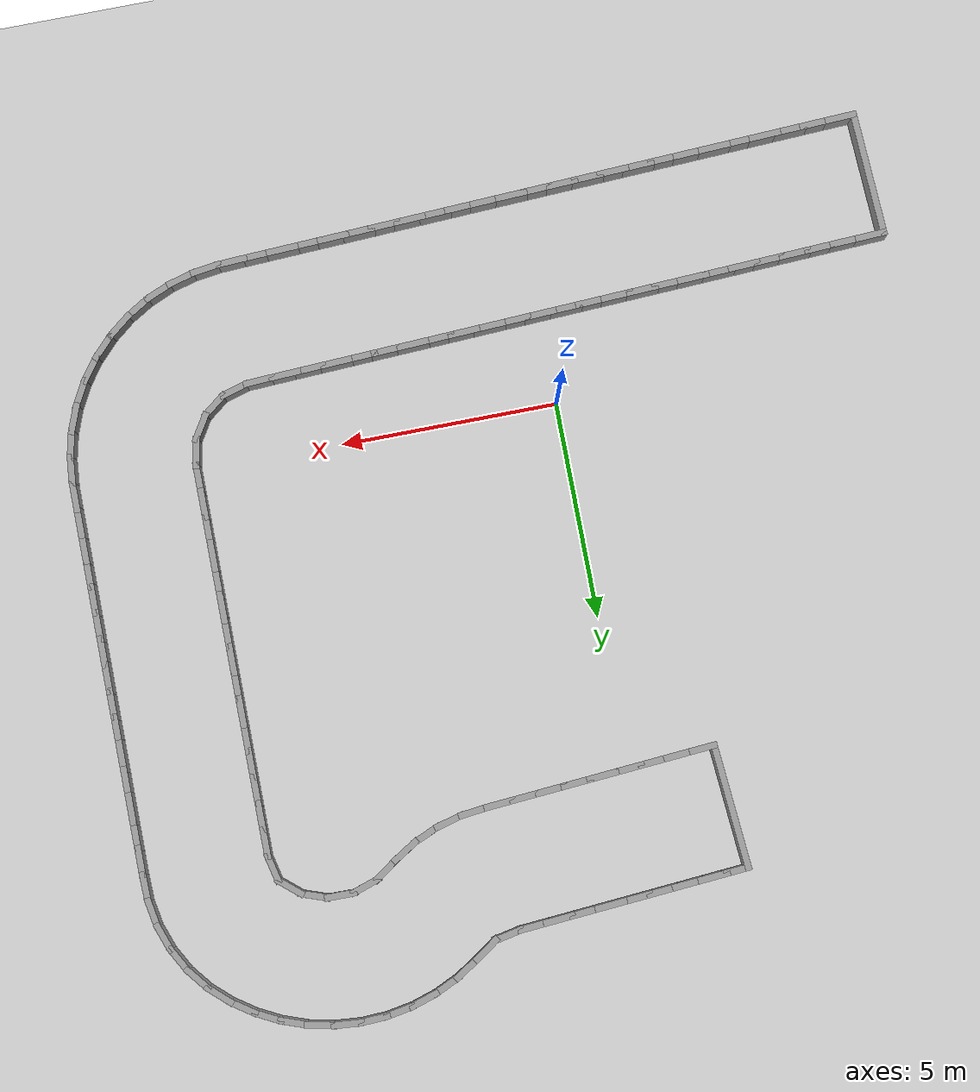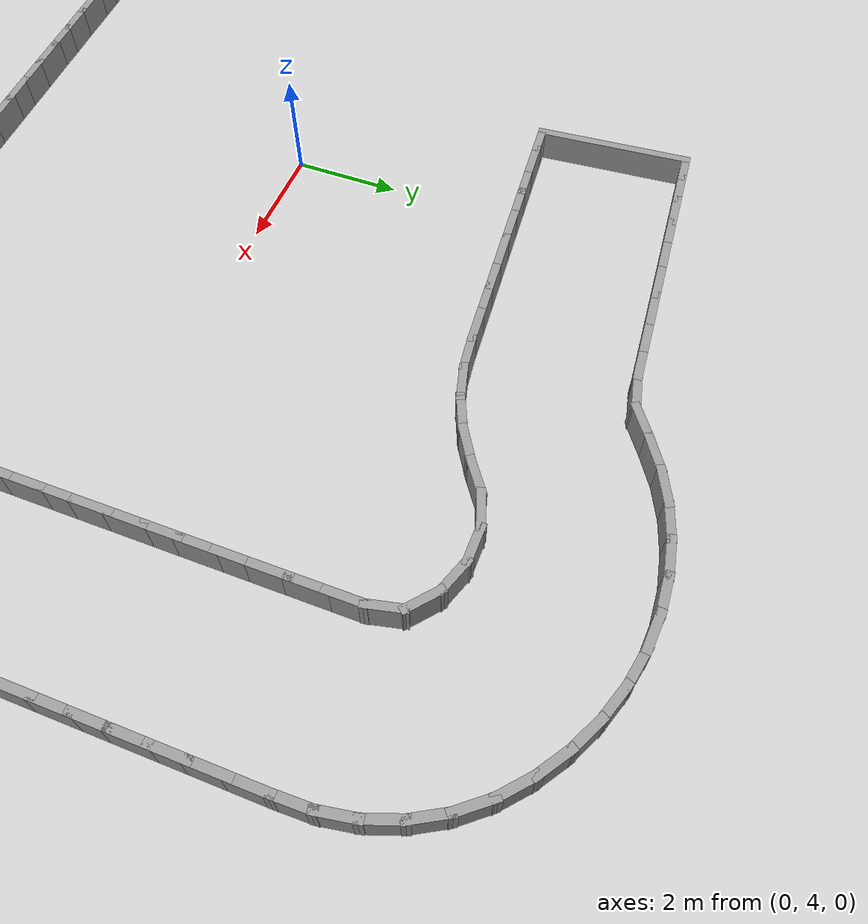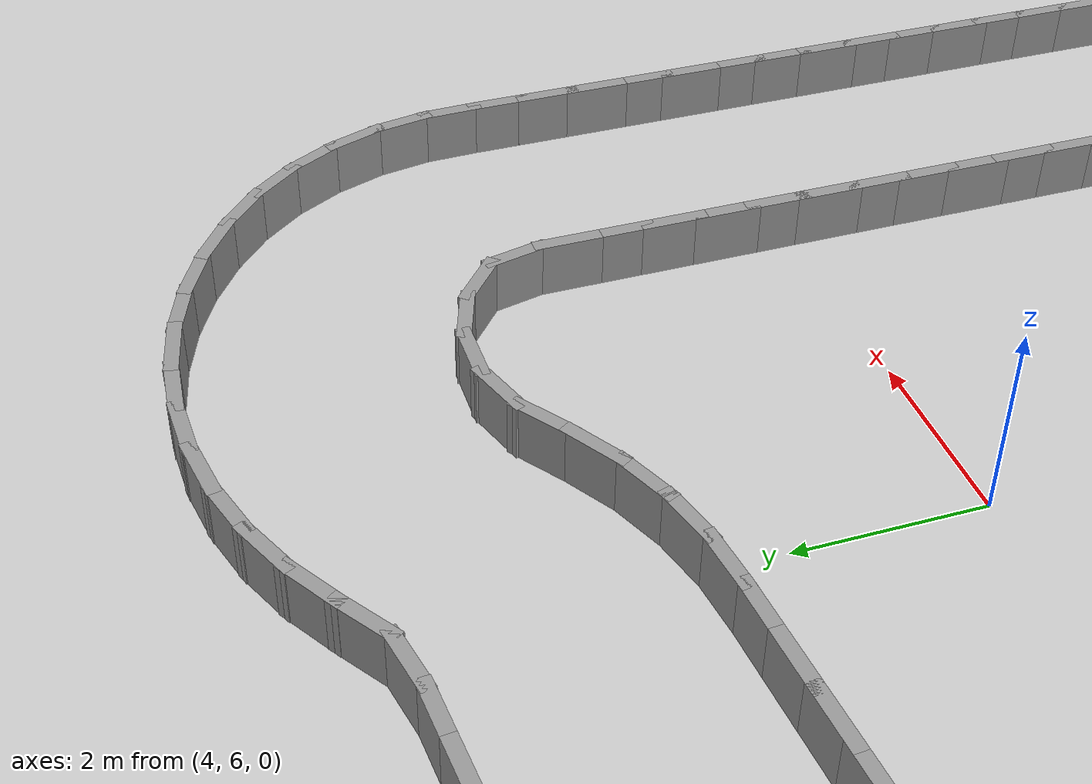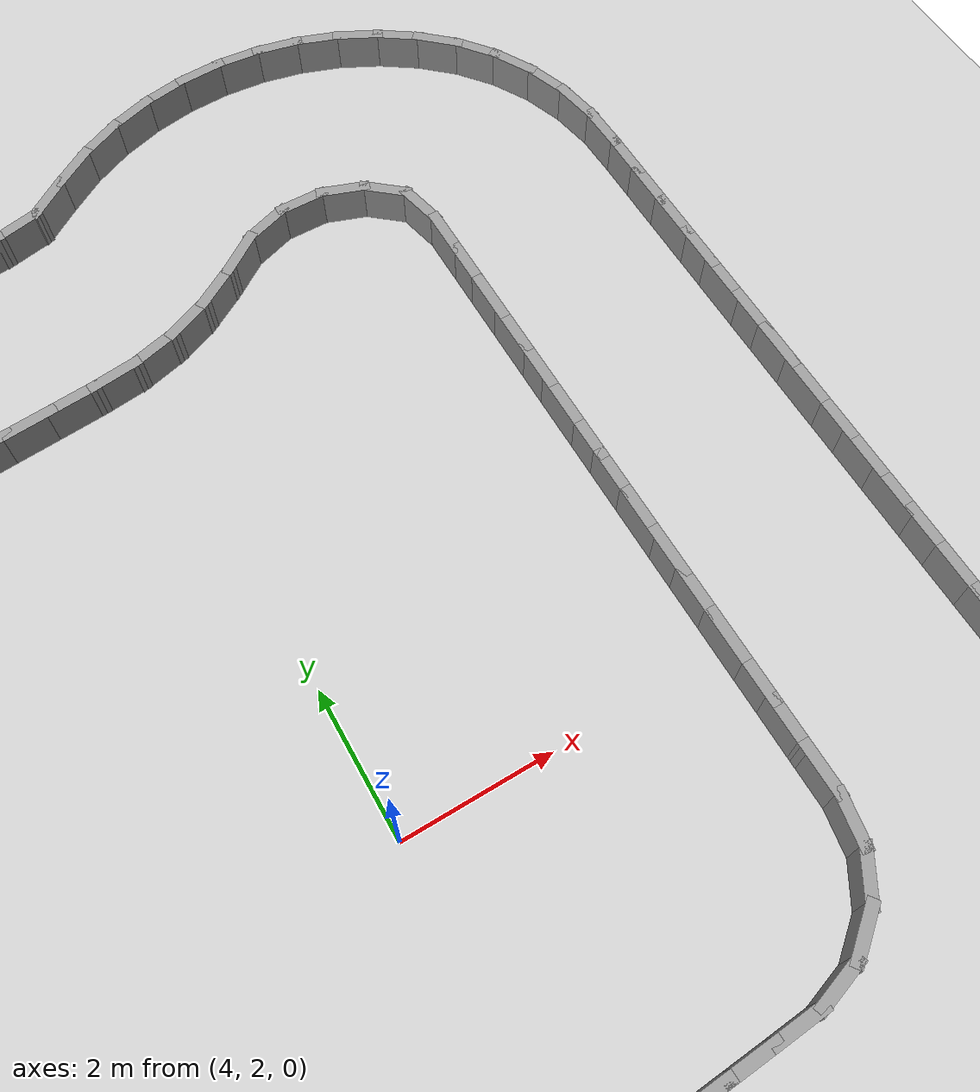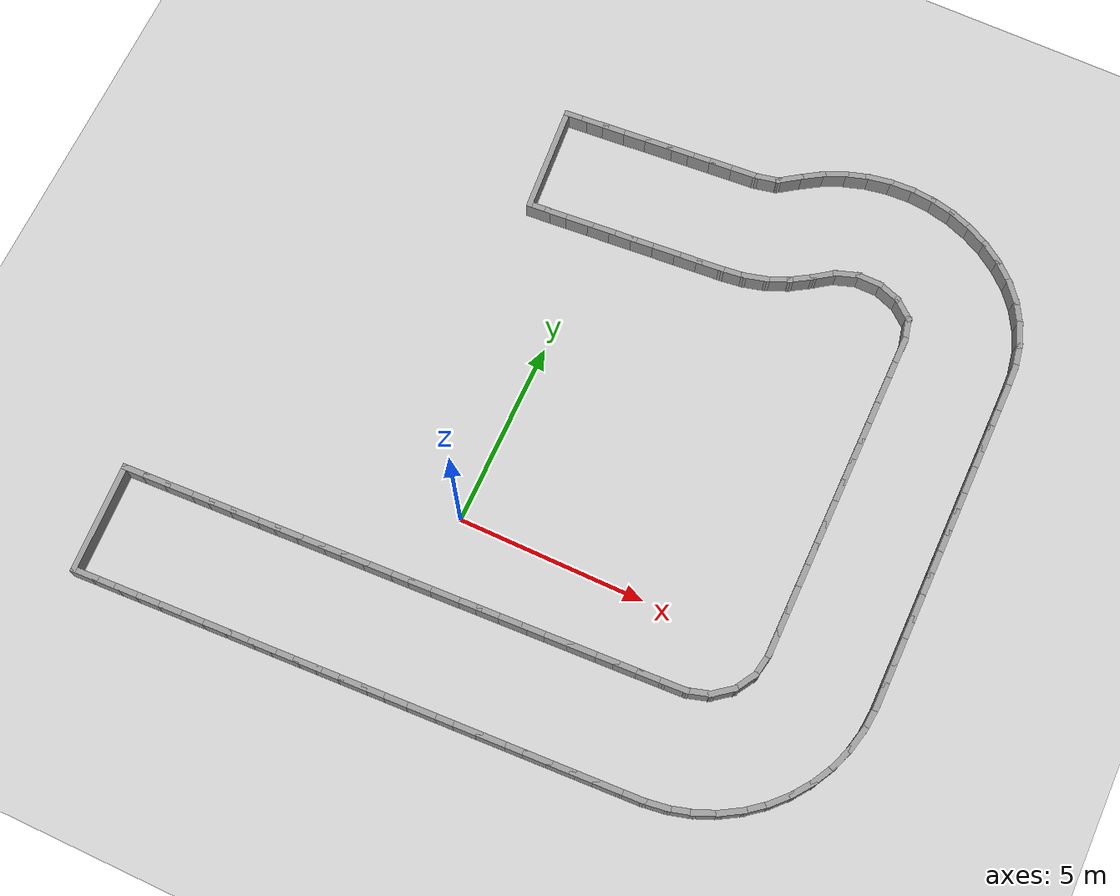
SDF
<?xml version="1.0" ?>
<sdf version='1.7'>
  <world name='default'>
    <plugin name='gazebo_ros_state' filename='libgazebo_ros_state.so'>
      <ros>
        <namespace>/</namespace>
      </ros>
      <update_rate>1000.0</update_rate>
    </plugin>

    <light name='sun' type='directional'>
      <cast_shadows>1</cast_shadows>
      <pose>0 0 10 0 -0 0</pose>
      <diffuse>0.8 0.8 0.8 1</diffuse>
      <specular>0.2 0.2 0.2 1</specular>
      <attenuation>
        <range>1000</range>
        <constant>0.9</constant>
        <linear>0.01</linear>
        <quadratic>0.001</quadratic>
      </attenuation>
      <direction>-0.5 0.1 -0.9</direction>
      <spot>
        <inner_angle>0</inner_angle>
        <outer_angle>0</outer_angle>
        <falloff>0</falloff>
      </spot>
    </light>
    <model name='ground_plane'>
      <static>1</static>
      <link name='link'>
        <collision name='collision'>
          <geometry>
            <plane>
              <normal>0 0 1</normal>
              <size>100 100</size>
            </plane>
          </geometry>
          <surface>
            <friction>
              <ode>
                <mu>100</mu>
                <mu2>50</mu2>
              </ode>
              <torsional>
                <ode/>
              </torsional>
            </friction>
            <contact>
              <ode/>
            </contact>
            <bounce/>
          </surface>
          <max_contacts>10</max_contacts>
        </collision>
        <visual name='visual'>
          <cast_shadows>0</cast_shadows>
          <geometry>
            <plane>
              <normal>0 0 1</normal>
              <size>100 100</size>
            </plane>
          </geometry>
          <material>
            <script>
              <uri>file://media/materials/scripts/gazebo.material</uri>
              <name>Gazebo/Grey</name>
            </script>
          </material>
        </visual>
        <self_collide>0</self_collide>
        <enable_wind>0</enable_wind>
        <kinematic>0</kinematic>
      </link>
    </model>
    <gravity>0 0 -9.8</gravity>
    <magnetic_field>6e-06 2.3e-05 -4.2e-05</magnetic_field>
    <atmosphere type='adiabatic'/>
    <physics type='ode'>
      <max_step_size>0.001</max_step_size>
      <real_time_factor>1</real_time_factor>
      <real_time_update_rate>1000</real_time_update_rate>
    </physics>
    <scene>
      <ambient>0.4 0.4 0.4 1</ambient>
      <background>0.7 0.7 0.7 1</background>
      <shadows>1</shadows>
    </scene>
    <audio>
      <device>default</device>
    </audio>
    <wind/>
    <spherical_coordinates>
      <surface_model>EARTH_WGS84</surface_model>
      <latitude_deg>0</latitude_deg>
      <longitude_deg>0</longitude_deg>
      <elevation>0</elevation>
      <heading_deg>0</heading_deg>
    </spherical_coordinates>
  <model name='rand_turn_09'>
    <pose>0 0 0 0 -0 0</pose>
    <link name='Wall_0'>
      <collision name='Wall_0_Collision'>
        <geometry><box><size>0.7500 0.1500 0.6000</size></box></geometry>
        <pose>0 0 0.3000 0 -0 0</pose>
      </collision>
      <visual name='Wall_0_Visual'>
        <pose>0 0 0.3000 0 -0 0</pose>
        <geometry><box><size>0.7500 0.1500 0.6000</size></box></geometry>
        <material>
          <script>
            <uri>file://media/materials/scripts/gazebo.material</uri>
            <name>Gazebo/Grey</name>
          </script>
          <ambient>1 1 1 1</ambient>
        </material>
      </visual>
      <pose>-7.8035 -2.3943 0 0 -0 0.04657</pose>
    </link>
    <link name='Wall_1'>
      <collision name='Wall_1_Collision'>
        <geometry><box><size>0.7500 0.1500 0.6000</size></box></geometry>
        <pose>0 0 0.3000 0 -0 0</pose>
      </collision>
      <visual name='Wall_1_Visual'>
        <pose>0 0 0.3000 0 -0 0</pose>
        <geometry><box><size>0.7500 0.1500 0.6000</size></box></geometry>
        <material>
          <script>
            <uri>file://media/materials/scripts/gazebo.material</uri>
            <name>Gazebo/Grey</name>
          </script>
          <ambient>1 1 1 1</ambient>
        </material>
      </visual>
      <pose>-7.2041 -2.3664 0 0 -0 0.04657</pose>
    </link>
    <link name='Wall_2'>
      <collision name='Wall_2_Collision'>
        <geometry><box><size>0.7500 0.1500 0.6000</size></box></geometry>
        <pose>0 0 0.3000 0 -0 0</pose>
      </collision>
      <visual name='Wall_2_Visual'>
        <pose>0 0 0.3000 0 -0 0</pose>
        <geometry><box><size>0.7500 0.1500 0.6000</size></box></geometry>
        <material>
          <script>
            <uri>file://media/materials/scripts/gazebo.material</uri>
            <name>Gazebo/Grey</name>
          </script>
          <ambient>1 1 1 1</ambient>
        </material>
      </visual>
      <pose>-6.6048 -2.3385 0 0 -0 0.04657</pose>
    </link>
    <link name='Wall_3'>
      <collision name='Wall_3_Collision'>
        <geometry><box><size>0.7500 0.1500 0.6000</size></box></geometry>
        <pose>0 0 0.3000 0 -0 0</pose>
      </collision>
      <visual name='Wall_3_Visual'>
        <pose>0 0 0.3000 0 -0 0</pose>
        <geometry><box><size>0.7500 0.1500 0.6000</size></box></geometry>
        <material>
          <script>
            <uri>file://media/materials/scripts/gazebo.material</uri>
            <name>Gazebo/Grey</name>
          </script>
          <ambient>1 1 1 1</ambient>
        </material>
      </visual>
      <pose>-6.0054 -2.3105 0 0 -0 0.04657</pose>
    </link>
    <link name='Wall_4'>
      <collision name='Wall_4_Collision'>
        <geometry><box><size>0.7500 0.1500 0.6000</size></box></geometry>
        <pose>0 0 0.3000 0 -0 0</pose>
      </collision>
      <visual name='Wall_4_Visual'>
        <pose>0 0 0.3000 0 -0 0</pose>
        <geometry><box><size>0.7500 0.1500 0.6000</size></box></geometry>
        <material>
          <script>
            <uri>file://media/materials/scripts/gazebo.material</uri>
            <name>Gazebo/Grey</name>
          </script>
          <ambient>1 1 1 1</ambient>
        </material>
      </visual>
      <pose>-5.4061 -2.2826 0 0 -0 0.04657</pose>
    </link>
    <link name='Wall_5'>
      <collision name='Wall_5_Collision'>
        <geometry><box><size>0.7500 0.1500 0.6000</size></box></geometry>
        <pose>0 0 0.3000 0 -0 0</pose>
      </collision>
      <visual name='Wall_5_Visual'>
        <pose>0 0 0.3000 0 -0 0</pose>
        <geometry><box><size>0.7500 0.1500 0.6000</size></box></geometry>
        <material>
          <script>
            <uri>file://media/materials/scripts/gazebo.material</uri>
            <name>Gazebo/Grey</name>
          </script>
          <ambient>1 1 1 1</ambient>
        </material>
      </visual>
      <pose>-4.8067 -2.2547 0 0 -0 0.04657</pose>
    </link>
    <link name='Wall_6'>
      <collision name='Wall_6_Collision'>
        <geometry><box><size>0.7500 0.1500 0.6000</size></box></geometry>
        <pose>0 0 0.3000 0 -0 0</pose>
      </collision>
      <visual name='Wall_6_Visual'>
        <pose>0 0 0.3000 0 -0 0</pose>
        <geometry><box><size>0.7500 0.1500 0.6000</size></box></geometry>
        <material>
          <script>
            <uri>file://media/materials/scripts/gazebo.material</uri>
            <name>Gazebo/Grey</name>
          </script>
          <ambient>1 1 1 1</ambient>
        </material>
      </visual>
      <pose>-4.2074 -2.2267 0 0 -0 0.04657</pose>
    </link>
    <link name='Wall_7'>
      <collision name='Wall_7_Collision'>
        <geometry><box><size>0.7500 0.1500 0.6000</size></box></geometry>
        <pose>0 0 0.3000 0 -0 0</pose>
      </collision>
      <visual name='Wall_7_Visual'>
        <pose>0 0 0.3000 0 -0 0</pose>
        <geometry><box><size>0.7500 0.1500 0.6000</size></box></geometry>
        <material>
          <script>
            <uri>file://media/materials/scripts/gazebo.material</uri>
            <name>Gazebo/Grey</name>
          </script>
          <ambient>1 1 1 1</ambient>
        </material>
      </visual>
      <pose>-3.6080 -2.1988 0 0 -0 0.04657</pose>
    </link>
    <link name='Wall_8'>
      <collision name='Wall_8_Collision'>
        <geometry><box><size>0.7500 0.1500 0.6000</size></box></geometry>
        <pose>0 0 0.3000 0 -0 0</pose>
      </collision>
      <visual name='Wall_8_Visual'>
        <pose>0 0 0.3000 0 -0 0</pose>
        <geometry><box><size>0.7500 0.1500 0.6000</size></box></geometry>
        <material>
          <script>
            <uri>file://media/materials/scripts/gazebo.material</uri>
            <name>Gazebo/Grey</name>
          </script>
          <ambient>1 1 1 1</ambient>
        </material>
      </visual>
      <pose>-3.0087 -2.1709 0 0 -0 0.04657</pose>
    </link>
    <link name='Wall_9'>
      <collision name='Wall_9_Collision'>
        <geometry><box><size>0.7500 0.1500 0.6000</size></box></geometry>
        <pose>0 0 0.3000 0 -0 0</pose>
      </collision>
      <visual name='Wall_9_Visual'>
        <pose>0 0 0.3000 0 -0 0</pose>
        <geometry><box><size>0.7500 0.1500 0.6000</size></box></geometry>
        <material>
          <script>
            <uri>file://media/materials/scripts/gazebo.material</uri>
            <name>Gazebo/Grey</name>
          </script>
          <ambient>1 1 1 1</ambient>
        </material>
      </visual>
      <pose>-2.4093 -2.1429 0 0 -0 0.04657</pose>
    </link>
    <link name='Wall_10'>
      <collision name='Wall_10_Collision'>
        <geometry><box><size>0.7500 0.1500 0.6000</size></box></geometry>
        <pose>0 0 0.3000 0 -0 0</pose>
      </collision>
      <visual name='Wall_10_Visual'>
        <pose>0 0 0.3000 0 -0 0</pose>
        <geometry><box><size>0.7500 0.1500 0.6000</size></box></geometry>
        <material>
          <script>
            <uri>file://media/materials/scripts/gazebo.material</uri>
            <name>Gazebo/Grey</name>
          </script>
          <ambient>1 1 1 1</ambient>
        </material>
      </visual>
      <pose>-1.8100 -2.1150 0 0 -0 0.04657</pose>
    </link>
    <link name='Wall_11'>
      <collision name='Wall_11_Collision'>
        <geometry><box><size>0.7500 0.1500 0.6000</size></box></geometry>
        <pose>0 0 0.3000 0 -0 0</pose>
      </collision>
      <visual name='Wall_11_Visual'>
        <pose>0 0 0.3000 0 -0 0</pose>
        <geometry><box><size>0.7500 0.1500 0.6000</size></box></geometry>
        <material>
          <script>
            <uri>file://media/materials/scripts/gazebo.material</uri>
            <name>Gazebo/Grey</name>
          </script>
          <ambient>1 1 1 1</ambient>
        </material>
      </visual>
      <pose>-1.2106 -2.0871 0 0 -0 0.04657</pose>
    </link>
    <link name='Wall_12'>
      <collision name='Wall_12_Collision'>
        <geometry><box><size>0.7500 0.1500 0.6000</size></box></geometry>
        <pose>0 0 0.3000 0 -0 0</pose>
      </collision>
      <visual name='Wall_12_Visual'>
        <pose>0 0 0.3000 0 -0 0</pose>
        <geometry><box><size>0.7500 0.1500 0.6000</size></box></geometry>
        <material>
          <script>
            <uri>file://media/materials/scripts/gazebo.material</uri>
            <name>Gazebo/Grey</name>
          </script>
          <ambient>1 1 1 1</ambient>
        </material>
      </visual>
      <pose>-0.6113 -2.0591 0 0 -0 0.04657</pose>
    </link>
    <link name='Wall_13'>
      <collision name='Wall_13_Collision'>
        <geometry><box><size>0.7500 0.1500 0.6000</size></box></geometry>
        <pose>0 0 0.3000 0 -0 0</pose>
      </collision>
      <visual name='Wall_13_Visual'>
        <pose>0 0 0.3000 0 -0 0</pose>
        <geometry><box><size>0.7500 0.1500 0.6000</size></box></geometry>
        <material>
          <script>
            <uri>file://media/materials/scripts/gazebo.material</uri>
            <name>Gazebo/Grey</name>
          </script>
          <ambient>1 1 1 1</ambient>
        </material>
      </visual>
      <pose>-0.0119 -2.0312 0 0 -0 0.04657</pose>
    </link>
    <link name='Wall_14'>
      <collision name='Wall_14_Collision'>
        <geometry><box><size>0.7500 0.1500 0.6000</size></box></geometry>
        <pose>0 0 0.3000 0 -0 0</pose>
      </collision>
      <visual name='Wall_14_Visual'>
        <pose>0 0 0.3000 0 -0 0</pose>
        <geometry><box><size>0.7500 0.1500 0.6000</size></box></geometry>
        <material>
          <script>
            <uri>file://media/materials/scripts/gazebo.material</uri>
            <name>Gazebo/Grey</name>
          </script>
          <ambient>1 1 1 1</ambient>
        </material>
      </visual>
      <pose>0.5874 -2.0033 0 0 -0 0.04657</pose>
    </link>
    <link name='Wall_15'>
      <collision name='Wall_15_Collision'>
        <geometry><box><size>0.7500 0.1500 0.6000</size></box></geometry>
        <pose>0 0 0.3000 0 -0 0</pose>
      </collision>
      <visual name='Wall_15_Visual'>
        <pose>0 0 0.3000 0 -0 0</pose>
        <geometry><box><size>0.7500 0.1500 0.6000</size></box></geometry>
        <material>
          <script>
            <uri>file://media/materials/scripts/gazebo.material</uri>
            <name>Gazebo/Grey</name>
          </script>
          <ambient>1 1 1 1</ambient>
        </material>
      </visual>
      <pose>1.1868 -1.9753 0 0 -0 0.04657</pose>
    </link>
    <link name='Wall_16'>
      <collision name='Wall_16_Collision'>
        <geometry><box><size>0.7500 0.1500 0.6000</size></box></geometry>
        <pose>0 0 0.3000 0 -0 0</pose>
      </collision>
      <visual name='Wall_16_Visual'>
        <pose>0 0 0.3000 0 -0 0</pose>
        <geometry><box><size>0.7500 0.1500 0.6000</size></box></geometry>
        <material>
          <script>
            <uri>file://media/materials/scripts/gazebo.material</uri>
            <name>Gazebo/Grey</name>
          </script>
          <ambient>1 1 1 1</ambient>
        </material>
      </visual>
      <pose>1.7861 -1.9474 0 0 -0 0.04657</pose>
    </link>
    <link name='Wall_17'>
      <collision name='Wall_17_Collision'>
        <geometry><box><size>0.7500 0.1500 0.6000</size></box></geometry>
        <pose>0 0 0.3000 0 -0 0</pose>
      </collision>
      <visual name='Wall_17_Visual'>
        <pose>0 0 0.3000 0 -0 0</pose>
        <geometry><box><size>0.7500 0.1500 0.6000</size></box></geometry>
        <material>
          <script>
            <uri>file://media/materials/scripts/gazebo.material</uri>
            <name>Gazebo/Grey</name>
          </script>
          <ambient>1 1 1 1</ambient>
        </material>
      </visual>
      <pose>2.3855 -1.9195 0 0 -0 0.04657</pose>
    </link>
    <link name='Wall_18'>
      <collision name='Wall_18_Collision'>
        <geometry><box><size>0.7500 0.1500 0.6000</size></box></geometry>
        <pose>0 0 0.3000 0 -0 0</pose>
      </collision>
      <visual name='Wall_18_Visual'>
        <pose>0 0 0.3000 0 -0 0</pose>
        <geometry><box><size>0.7500 0.1500 0.6000</size></box></geometry>
        <material>
          <script>
            <uri>file://media/materials/scripts/gazebo.material</uri>
            <name>Gazebo/Grey</name>
          </script>
          <ambient>1 1 1 1</ambient>
        </material>
      </visual>
      <pose>2.9848 -1.8915 0 0 -0 0.04657</pose>
    </link>
    <link name='Wall_19'>
      <collision name='Wall_19_Collision'>
        <geometry><box><size>0.7500 0.1500 0.6000</size></box></geometry>
        <pose>0 0 0.3000 0 -0 0</pose>
      </collision>
      <visual name='Wall_19_Visual'>
        <pose>0 0 0.3000 0 -0 0</pose>
        <geometry><box><size>0.7500 0.1500 0.6000</size></box></geometry>
        <material>
          <script>
            <uri>file://media/materials/scripts/gazebo.material</uri>
            <name>Gazebo/Grey</name>
          </script>
          <ambient>1 1 1 1</ambient>
        </material>
      </visual>
      <pose>3.5842 -1.8636 0 0 -0 0.04657</pose>
    </link>
    <link name='Wall_20'>
      <collision name='Wall_20_Collision'>
        <geometry><box><size>0.7500 0.1500 0.6000</size></box></geometry>
        <pose>0 0 0.3000 0 -0 0</pose>
      </collision>
      <visual name='Wall_20_Visual'>
        <pose>0 0 0.3000 0 -0 0</pose>
        <geometry><box><size>0.7500 0.1500 0.6000</size></box></geometry>
        <material>
          <script>
            <uri>file://media/materials/scripts/gazebo.material</uri>
            <name>Gazebo/Grey</name>
          </script>
          <ambient>1 1 1 1</ambient>
        </material>
      </visual>
      <pose>4.1835 -1.8357 0 0 -0 0.04657</pose>
    </link>
    <link name='Wall_21'>
      <collision name='Wall_21_Collision'>
        <geometry><box><size>0.7500 0.1500 0.6000</size></box></geometry>
        <pose>0 0 0.3000 0 -0 0</pose>
      </collision>
      <visual name='Wall_21_Visual'>
        <pose>0 0 0.3000 0 -0 0</pose>
        <geometry><box><size>0.7500 0.1500 0.6000</size></box></geometry>
        <material>
          <script>
            <uri>file://media/materials/scripts/gazebo.material</uri>
            <name>Gazebo/Grey</name>
          </script>
          <ambient>1 1 1 1</ambient>
        </material>
      </visual>
      <pose>4.7829 -1.8077 0 0 -0 0.04657</pose>
    </link>
    <link name='Wall_22'>
      <collision name='Wall_22_Collision'>
        <geometry><box><size>0.7500 0.1500 0.6000</size></box></geometry>
        <pose>0 0 0.3000 0 -0 0</pose>
      </collision>
      <visual name='Wall_22_Visual'>
        <pose>0 0 0.3000 0 -0 0</pose>
        <geometry><box><size>0.7500 0.1500 0.6000</size></box></geometry>
        <material>
          <script>
            <uri>file://media/materials/scripts/gazebo.material</uri>
            <name>Gazebo/Grey</name>
          </script>
          <ambient>1 1 1 1</ambient>
        </material>
      </visual>
      <pose>5.3822 -1.7798 0 0 -0 0.04657</pose>
    </link>
    <link name='Wall_23'>
      <collision name='Wall_23_Collision'>
        <geometry><box><size>0.7500 0.1500 0.6000</size></box></geometry>
        <pose>0 0 0.3000 0 -0 0</pose>
      </collision>
      <visual name='Wall_23_Visual'>
        <pose>0 0 0.3000 0 -0 0</pose>
        <geometry><box><size>0.7500 0.1500 0.6000</size></box></geometry>
        <material>
          <script>
            <uri>file://media/materials/scripts/gazebo.material</uri>
            <name>Gazebo/Grey</name>
          </script>
          <ambient>1 1 1 1</ambient>
        </material>
      </visual>
      <pose>5.9816 -1.7519 0 0 -0 0.04657</pose>
    </link>
    <link name='Wall_24'>
      <collision name='Wall_24_Collision'>
        <geometry><box><size>0.7499 0.1500 0.6000</size></box></geometry>
        <pose>0 0 0.3000 0 -0 0</pose>
      </collision>
      <visual name='Wall_24_Visual'>
        <pose>0 0 0.3000 0 -0 0</pose>
        <geometry><box><size>0.7499 0.1500 0.6000</size></box></geometry>
        <material>
          <script>
            <uri>file://media/materials/scripts/gazebo.material</uri>
            <name>Gazebo/Grey</name>
          </script>
          <ambient>1 1 1 1</ambient>
        </material>
      </visual>
      <pose>6.5808 -1.7224 0 0 -0 0.05183</pose>
    </link>
    <link name='Wall_25'>
      <collision name='Wall_25_Collision'>
        <geometry><box><size>0.7467 0.1500 0.6000</size></box></geometry>
        <pose>0 0 0.3000 0 -0 0</pose>
      </collision>
      <visual name='Wall_25_Visual'>
        <pose>0 0 0.3000 0 -0 0</pose>
        <geometry><box><size>0.7467 0.1500 0.6000</size></box></geometry>
        <material>
          <script>
            <uri>file://media/materials/scripts/gazebo.material</uri>
            <name>Gazebo/Grey</name>
          </script>
          <ambient>1 1 1 1</ambient>
        </material>
      </visual>
      <pose>7.1662 -1.6213 0 0 -0 0.29063</pose>
    </link>
    <link name='Wall_26'>
      <collision name='Wall_26_Collision'>
        <geometry><box><size>0.7466 0.1500 0.6000</size></box></geometry>
        <pose>0 0 0.3000 0 -0 0</pose>
      </collision>
      <visual name='Wall_26_Visual'>
        <pose>0 0 0.3000 0 -0 0</pose>
        <geometry><box><size>0.7466 0.1500 0.6000</size></box></geometry>
        <material>
          <script>
            <uri>file://media/materials/scripts/gazebo.material</uri>
            <name>Gazebo/Grey</name>
          </script>
          <ambient>1 1 1 1</ambient>
        </material>
      </visual>
      <pose>7.6882 -1.3536 0 0 -0 0.65714</pose>
    </link>
    <link name='Wall_27'>
      <collision name='Wall_27_Collision'>
        <geometry><box><size>0.7466 0.1500 0.6000</size></box></geometry>
        <pose>0 0 0.3000 0 -0 0</pose>
      </collision>
      <visual name='Wall_27_Visual'>
        <pose>0 0 0.3000 0 -0 0</pose>
        <geometry><box><size>0.7466 0.1500 0.6000</size></box></geometry>
        <material>
          <script>
            <uri>file://media/materials/scripts/gazebo.material</uri>
            <name>Gazebo/Grey</name>
          </script>
          <ambient>1 1 1 1</ambient>
        </material>
      </visual>
      <pose>8.0797 -0.9167 0 0 -0 1.02326</pose>
    </link>
    <link name='Wall_28'>
      <collision name='Wall_28_Collision'>
        <geometry><box><size>0.7466 0.1500 0.6000</size></box></geometry>
        <pose>0 0 0.3000 0 -0 0</pose>
      </collision>
      <visual name='Wall_28_Visual'>
        <pose>0 0 0.3000 0 -0 0</pose>
        <geometry><box><size>0.7466 0.1500 0.6000</size></box></geometry>
        <material>
          <script>
            <uri>file://media/materials/scripts/gazebo.material</uri>
            <name>Gazebo/Grey</name>
          </script>
          <ambient>1 1 1 1</ambient>
        </material>
      </visual>
      <pose>8.2887 -0.3686 0 0 -0 1.38976</pose>
    </link>
    <link name='Wall_29'>
      <collision name='Wall_29_Collision'>
        <geometry><box><size>0.7500 0.1500 0.6000</size></box></geometry>
        <pose>0 0 0.3000 0 -0 0</pose>
      </collision>
      <visual name='Wall_29_Visual'>
        <pose>0 0 0.3000 0 -0 0</pose>
        <geometry><box><size>0.7500 0.1500 0.6000</size></box></geometry>
        <material>
          <script>
            <uri>file://media/materials/scripts/gazebo.material</uri>
            <name>Gazebo/Grey</name>
          </script>
          <ambient>1 1 1 1</ambient>
        </material>
      </visual>
      <pose>8.3423 0.2248 0 0 -0 1.57105</pose>
    </link>
    <link name='Wall_30'>
      <collision name='Wall_30_Collision'>
        <geometry><box><size>0.7500 0.1500 0.6000</size></box></geometry>
        <pose>0 0 0.3000 0 -0 0</pose>
      </collision>
      <visual name='Wall_30_Visual'>
        <pose>0 0 0.3000 0 -0 0</pose>
        <geometry><box><size>0.7500 0.1500 0.6000</size></box></geometry>
        <material>
          <script>
            <uri>file://media/materials/scripts/gazebo.material</uri>
            <name>Gazebo/Grey</name>
          </script>
          <ambient>1 1 1 1</ambient>
        </material>
      </visual>
      <pose>8.3422 0.8248 0 0 -0 1.57086</pose>
    </link>
    <link name='Wall_31'>
      <collision name='Wall_31_Collision'>
        <geometry><box><size>0.7500 0.1500 0.6000</size></box></geometry>
        <pose>0 0 0.3000 0 -0 0</pose>
      </collision>
      <visual name='Wall_31_Visual'>
        <pose>0 0 0.3000 0 -0 0</pose>
        <geometry><box><size>0.7500 0.1500 0.6000</size></box></geometry>
        <material>
          <script>
            <uri>file://media/materials/scripts/gazebo.material</uri>
            <name>Gazebo/Grey</name>
          </script>
          <ambient>1 1 1 1</ambient>
        </material>
      </visual>
      <pose>8.3422 1.4248 0 0 -0 1.57086</pose>
    </link>
    <link name='Wall_32'>
      <collision name='Wall_32_Collision'>
        <geometry><box><size>0.7500 0.1500 0.6000</size></box></geometry>
        <pose>0 0 0.3000 0 -0 0</pose>
      </collision>
      <visual name='Wall_32_Visual'>
        <pose>0 0 0.3000 0 -0 0</pose>
        <geometry><box><size>0.7500 0.1500 0.6000</size></box></geometry>
        <material>
          <script>
            <uri>file://media/materials/scripts/gazebo.material</uri>
            <name>Gazebo/Grey</name>
          </script>
          <ambient>1 1 1 1</ambient>
        </material>
      </visual>
      <pose>8.3421 2.0248 0 0 -0 1.57086</pose>
    </link>
    <link name='Wall_33'>
      <collision name='Wall_33_Collision'>
        <geometry><box><size>0.7500 0.1500 0.6000</size></box></geometry>
        <pose>0 0 0.3000 0 -0 0</pose>
      </collision>
      <visual name='Wall_33_Visual'>
        <pose>0 0 0.3000 0 -0 0</pose>
        <geometry><box><size>0.7500 0.1500 0.6000</size></box></geometry>
        <material>
          <script>
            <uri>file://media/materials/scripts/gazebo.material</uri>
            <name>Gazebo/Grey</name>
          </script>
          <ambient>1 1 1 1</ambient>
        </material>
      </visual>
      <pose>8.3421 2.6248 0 0 -0 1.57086</pose>
    </link>
    <link name='Wall_34'>
      <collision name='Wall_34_Collision'>
        <geometry><box><size>0.7500 0.1500 0.6000</size></box></geometry>
        <pose>0 0 0.3000 0 -0 0</pose>
      </collision>
      <visual name='Wall_34_Visual'>
        <pose>0 0 0.3000 0 -0 0</pose>
        <geometry><box><size>0.7500 0.1500 0.6000</size></box></geometry>
        <material>
          <script>
            <uri>file://media/materials/scripts/gazebo.material</uri>
            <name>Gazebo/Grey</name>
          </script>
          <ambient>1 1 1 1</ambient>
        </material>
      </visual>
      <pose>8.3421 3.2248 0 0 -0 1.57086</pose>
    </link>
    <link name='Wall_35'>
      <collision name='Wall_35_Collision'>
        <geometry><box><size>0.7500 0.1500 0.6000</size></box></geometry>
        <pose>0 0 0.3000 0 -0 0</pose>
      </collision>
      <visual name='Wall_35_Visual'>
        <pose>0 0 0.3000 0 -0 0</pose>
        <geometry><box><size>0.7500 0.1500 0.6000</size></box></geometry>
        <material>
          <script>
            <uri>file://media/materials/scripts/gazebo.material</uri>
            <name>Gazebo/Grey</name>
          </script>
          <ambient>1 1 1 1</ambient>
        </material>
      </visual>
      <pose>8.3420 3.8248 0 0 -0 1.57086</pose>
    </link>
    <link name='Wall_36'>
      <collision name='Wall_36_Collision'>
        <geometry><box><size>0.7500 0.1500 0.6000</size></box></geometry>
        <pose>0 0 0.3000 0 -0 0</pose>
      </collision>
      <visual name='Wall_36_Visual'>
        <pose>0 0 0.3000 0 -0 0</pose>
        <geometry><box><size>0.7500 0.1500 0.6000</size></box></geometry>
        <material>
          <script>
            <uri>file://media/materials/scripts/gazebo.material</uri>
            <name>Gazebo/Grey</name>
          </script>
          <ambient>1 1 1 1</ambient>
        </material>
      </visual>
      <pose>8.3420 4.4248 0 0 -0 1.57086</pose>
    </link>
    <link name='Wall_37'>
      <collision name='Wall_37_Collision'>
        <geometry><box><size>0.7500 0.1500 0.6000</size></box></geometry>
        <pose>0 0 0.3000 0 -0 0</pose>
      </collision>
      <visual name='Wall_37_Visual'>
        <pose>0 0 0.3000 0 -0 0</pose>
        <geometry><box><size>0.7500 0.1500 0.6000</size></box></geometry>
        <material>
          <script>
            <uri>file://media/materials/scripts/gazebo.material</uri>
            <name>Gazebo/Grey</name>
          </script>
          <ambient>1 1 1 1</ambient>
        </material>
      </visual>
      <pose>8.3420 5.0248 0 0 -0 1.57086</pose>
    </link>
    <link name='Wall_38'>
      <collision name='Wall_38_Collision'>
        <geometry><box><size>0.7500 0.1500 0.6000</size></box></geometry>
        <pose>0 0 0.3000 0 -0 0</pose>
      </collision>
      <visual name='Wall_38_Visual'>
        <pose>0 0 0.3000 0 -0 0</pose>
        <geometry><box><size>0.7500 0.1500 0.6000</size></box></geometry>
        <material>
          <script>
            <uri>file://media/materials/scripts/gazebo.material</uri>
            <name>Gazebo/Grey</name>
          </script>
          <ambient>1 1 1 1</ambient>
        </material>
      </visual>
      <pose>8.3419 5.6248 0 0 -0 1.57086</pose>
    </link>
    <link name='Wall_39'>
      <collision name='Wall_39_Collision'>
        <geometry><box><size>0.7500 0.1500 0.6000</size></box></geometry>
        <pose>0 0 0.3000 0 -0 0</pose>
      </collision>
      <visual name='Wall_39_Visual'>
        <pose>0 0 0.3000 0 -0 0</pose>
        <geometry><box><size>0.7500 0.1500 0.6000</size></box></geometry>
        <material>
          <script>
            <uri>file://media/materials/scripts/gazebo.material</uri>
            <name>Gazebo/Grey</name>
          </script>
          <ambient>1 1 1 1</ambient>
        </material>
      </visual>
      <pose>8.3419 6.2248 0 0 -0 1.57086</pose>
    </link>
    <link name='Wall_40'>
      <collision name='Wall_40_Collision'>
        <geometry><box><size>0.7500 0.1500 0.6000</size></box></geometry>
        <pose>0 0 0.3000 0 -0 0</pose>
      </collision>
      <visual name='Wall_40_Visual'>
        <pose>0 0 0.3000 0 -0 0</pose>
        <geometry><box><size>0.7500 0.1500 0.6000</size></box></geometry>
        <material>
          <script>
            <uri>file://media/materials/scripts/gazebo.material</uri>
            <name>Gazebo/Grey</name>
          </script>
          <ambient>1 1 1 1</ambient>
        </material>
      </visual>
      <pose>8.3418 6.8248 0 0 -0 1.57086</pose>
    </link>
    <link name='Wall_41'>
      <collision name='Wall_41_Collision'>
        <geometry><box><size>0.7500 0.1500 0.6000</size></box></geometry>
        <pose>0 0 0.3000 0 -0 0</pose>
      </collision>
      <visual name='Wall_41_Visual'>
        <pose>0 0 0.3000 0 -0 0</pose>
        <geometry><box><size>0.7500 0.1500 0.6000</size></box></geometry>
        <material>
          <script>
            <uri>file://media/materials/scripts/gazebo.material</uri>
            <name>Gazebo/Grey</name>
          </script>
          <ambient>1 1 1 1</ambient>
        </material>
      </visual>
      <pose>8.3418 7.4248 0 0 -0 1.57086</pose>
    </link>
    <link name='Wall_42'>
      <collision name='Wall_42_Collision'>
        <geometry><box><size>0.7500 0.1500 0.6000</size></box></geometry>
        <pose>0 0 0.3000 0 -0 0</pose>
      </collision>
      <visual name='Wall_42_Visual'>
        <pose>0 0 0.3000 0 -0 0</pose>
        <geometry><box><size>0.7500 0.1500 0.6000</size></box></geometry>
        <material>
          <script>
            <uri>file://media/materials/scripts/gazebo.material</uri>
            <name>Gazebo/Grey</name>
          </script>
          <ambient>1 1 1 1</ambient>
        </material>
      </visual>
      <pose>8.3418 8.0248 0 0 -0 1.57086</pose>
    </link>
    <link name='Wall_43'>
      <collision name='Wall_43_Collision'>
        <geometry><box><size>0.7500 0.1500 0.6000</size></box></geometry>
        <pose>0 0 0.3000 0 -0 0</pose>
      </collision>
      <visual name='Wall_43_Visual'>
        <pose>0 0 0.3000 0 -0 0</pose>
        <geometry><box><size>0.7500 0.1500 0.6000</size></box></geometry>
        <material>
          <script>
            <uri>file://media/materials/scripts/gazebo.material</uri>
            <name>Gazebo/Grey</name>
          </script>
          <ambient>1 1 1 1</ambient>
        </material>
      </visual>
      <pose>8.3417 8.6248 0 0 -0 1.57086</pose>
    </link>
    <link name='Wall_44'>
      <collision name='Wall_44_Collision'>
        <geometry><box><size>0.7390 0.1500 0.6000</size></box></geometry>
        <pose>0 0 0.3000 0 -0 0</pose>
      </collision>
      <visual name='Wall_44_Visual'>
        <pose>0 0 0.3000 0 -0 0</pose>
        <geometry><box><size>0.7390 0.1500 0.6000</size></box></geometry>
        <material>
          <script>
            <uri>file://media/materials/scripts/gazebo.material</uri>
            <name>Gazebo/Grey</name>
          </script>
          <ambient>1 1 1 1</ambient>
        </material>
      </visual>
      <pose>8.2764 9.2120 0 0 -0 1.79442</pose>
    </link>
    <link name='Wall_45'>
      <collision name='Wall_45_Collision'>
        <geometry><box><size>0.7448 0.1500 0.6000</size></box></geometry>
        <pose>0 0 0.3000 0 -0 0</pose>
      </collision>
      <visual name='Wall_45_Visual'>
        <pose>0 0 0.3000 0 -0 0</pose>
        <geometry><box><size>0.7448 0.1500 0.6000</size></box></geometry>
        <material>
          <script>
            <uri>file://media/materials/scripts/gazebo.material</uri>
            <name>Gazebo/Grey</name>
          </script>
          <ambient>1 1 1 1</ambient>
        </material>
      </visual>
      <pose>7.9837 9.6908 0 0 -0 2.44117</pose>
    </link>
    <link name='Wall_46'>
      <collision name='Wall_46_Collision'>
        <geometry><box><size>0.7472 0.1500 0.6000</size></box></geometry>
        <pose>0 0 0.3000 0 -0 0</pose>
      </collision>
      <visual name='Wall_46_Visual'>
        <pose>0 0 0.3000 0 -0 0</pose>
        <geometry><box><size>0.7472 0.1500 0.6000</size></box></geometry>
        <material>
          <script>
            <uri>file://media/materials/scripts/gazebo.material</uri>
            <name>Gazebo/Grey</name>
          </script>
          <ambient>1 1 1 1</ambient>
        </material>
      </visual>
      <pose>7.4751 9.9829 0 0 -0 2.79888</pose>
    </link>
    <link name='Wall_47'>
      <collision name='Wall_47_Collision'>
        <geometry><box><size>0.7472 0.1500 0.6000</size></box></geometry>
        <pose>0 0 0.3000 0 -0 0</pose>
      </collision>
      <visual name='Wall_47_Visual'>
        <pose>0 0 0.3000 0 -0 0</pose>
        <geometry><box><size>0.7472 0.1500 0.6000</size></box></geometry>
        <material>
          <script>
            <uri>file://media/materials/scripts/gazebo.material</uri>
            <name>Gazebo/Grey</name>
          </script>
          <ambient>1 1 1 1</ambient>
        </material>
      </visual>
      <pose>6.8953 10.0859 0 0 -0 3.13249</pose>
    </link>
    <link name='Wall_48'>
      <collision name='Wall_48_Collision'>
        <geometry><box><size>0.7472 0.1500 0.6000</size></box></geometry>
        <pose>0 0 0.3000 0 -0 0</pose>
      </collision>
      <visual name='Wall_48_Visual'>
        <pose>0 0 0.3000 0 -0 0</pose>
        <geometry><box><size>0.7472 0.1500 0.6000</size></box></geometry>
        <material>
          <script>
            <uri>file://media/materials/scripts/gazebo.material</uri>
            <name>Gazebo/Grey</name>
          </script>
          <ambient>1 1 1 1</ambient>
        </material>
      </visual>
      <pose>6.3138 9.9933 0 0 -0 -2.81664</pose>
    </link>
    <link name='Wall_49'>
      <collision name='Wall_49_Collision'>
        <geometry><box><size>0.7491 0.1500 0.6000</size></box></geometry>
        <pose>0 0 0.3000 0 -0 0</pose>
      </collision>
      <visual name='Wall_49_Visual'>
        <pose>0 0 0.3000 0 -0 0</pose>
        <geometry><box><size>0.7491 0.1500 0.6000</size></box></geometry>
        <material>
          <script>
            <uri>file://media/materials/scripts/gazebo.material</uri>
            <name>Gazebo/Grey</name>
          </script>
          <ambient>1 1 1 1</ambient>
        </material>
      </visual>
      <pose>5.7865 9.7246 0 0 -0 -2.52444</pose>
    </link>
    <link name='Wall_50'>
      <collision name='Wall_50_Collision'>
        <geometry><box><size>0.7494 0.1500 0.6000</size></box></geometry>
        <pose>0 0 0.3000 0 -0 0</pose>
      </collision>
      <visual name='Wall_50_Visual'>
        <pose>0 0 0.3000 0 -0 0</pose>
        <geometry><box><size>0.7494 0.1500 0.6000</size></box></geometry>
        <material>
          <script>
            <uri>file://media/materials/scripts/gazebo.material</uri>
            <name>Gazebo/Grey</name>
          </script>
          <ambient>1 1 1 1</ambient>
        </material>
      </visual>
      <pose>5.2873 9.3937 0 0 -0 -2.58797</pose>
    </link>
    <link name='Wall_51'>
      <collision name='Wall_51_Collision'>
        <geometry><box><size>0.7494 0.1500 0.6000</size></box></geometry>
        <pose>0 0 0.3000 0 -0 0</pose>
      </collision>
      <visual name='Wall_51_Visual'>
        <pose>0 0 0.3000 0 -0 0</pose>
        <geometry><box><size>0.7494 0.1500 0.6000</size></box></geometry>
        <material>
          <script>
            <uri>file://media/materials/scripts/gazebo.material</uri>
            <name>Gazebo/Grey</name>
          </script>
          <ambient>1 1 1 1</ambient>
        </material>
      </visual>
      <pose>4.7570 9.1177 0 0 -0 -2.73549</pose>
    </link>
    <link name='Wall_52'>
      <collision name='Wall_52_Collision'>
        <geometry><box><size>0.7494 0.1500 0.6000</size></box></geometry>
        <pose>0 0 0.3000 0 -0 0</pose>
      </collision>
      <visual name='Wall_52_Visual'>
        <pose>0 0 0.3000 0 -0 0</pose>
        <geometry><box><size>0.7494 0.1500 0.6000</size></box></geometry>
        <material>
          <script>
            <uri>file://media/materials/scripts/gazebo.material</uri>
            <name>Gazebo/Grey</name>
          </script>
          <ambient>1 1 1 1</ambient>
        </material>
      </visual>
      <pose>4.1920 8.9227 0 0 -0 -2.88301</pose>
    </link>
    <link name='Wall_53'>
      <collision name='Wall_53_Collision'>
        <geometry><box><size>0.7496 0.1500 0.6000</size></box></geometry>
        <pose>0 0 0.3000 0 -0 0</pose>
      </collision>
      <visual name='Wall_53_Visual'>
        <pose>0 0 0.3000 0 -0 0</pose>
        <geometry><box><size>0.7496 0.1500 0.6000</size></box></geometry>
        <material>
          <script>
            <uri>file://media/materials/scripts/gazebo.material</uri>
            <name>Gazebo/Grey</name>
          </script>
          <ambient>1 1 1 1</ambient>
        </material>
      </visual>
      <pose>3.6045 8.8110 0 0 -0 -3.02437</pose>
    </link>
    <link name='Wall_54'>
      <collision name='Wall_54_Collision'>
        <geometry><box><size>0.7500 0.1500 0.6000</size></box></geometry>
        <pose>0 0 0.3000 0 -0 0</pose>
      </collision>
      <visual name='Wall_54_Visual'>
        <pose>0 0 0.3000 0 -0 0</pose>
        <geometry><box><size>0.7500 0.1500 0.6000</size></box></geometry>
        <material>
          <script>
            <uri>file://media/materials/scripts/gazebo.material</uri>
            <name>Gazebo/Grey</name>
          </script>
          <ambient>1 1 1 1</ambient>
        </material>
      </visual>
      <pose>3.0077 8.7528 0 0 -0 -3.06450</pose>
    </link>
    <link name='Wall_55'>
      <collision name='Wall_55_Collision'>
        <geometry><box><size>0.7500 0.1500 0.6000</size></box></geometry>
        <pose>0 0 0.3000 0 -0 0</pose>
      </collision>
      <visual name='Wall_55_Visual'>
        <pose>0 0 0.3000 0 -0 0</pose>
        <geometry><box><size>0.7500 0.1500 0.6000</size></box></geometry>
        <material>
          <script>
            <uri>file://media/materials/scripts/gazebo.material</uri>
            <name>Gazebo/Grey</name>
          </script>
          <ambient>1 1 1 1</ambient>
        </material>
      </visual>
      <pose>2.4095 8.7066 0 0 -0 -3.06450</pose>
    </link>
    <link name='Wall_56'>
      <collision name='Wall_56_Collision'>
        <geometry><box><size>0.7500 0.1500 0.6000</size></box></geometry>
        <pose>0 0 0.3000 0 -0 0</pose>
      </collision>
      <visual name='Wall_56_Visual'>
        <pose>0 0 0.3000 0 -0 0</pose>
        <geometry><box><size>0.7500 0.1500 0.6000</size></box></geometry>
        <material>
          <script>
            <uri>file://media/materials/scripts/gazebo.material</uri>
            <name>Gazebo/Grey</name>
          </script>
          <ambient>1 1 1 1</ambient>
        </material>
      </visual>
      <pose>1.8112 8.6604 0 0 -0 -3.06450</pose>
    </link>
    <link name='Wall_57'>
      <collision name='Wall_57_Collision'>
        <geometry><box><size>0.7500 0.1500 0.6000</size></box></geometry>
        <pose>0 0 0.3000 0 -0 0</pose>
      </collision>
      <visual name='Wall_57_Visual'>
        <pose>0 0 0.3000 0 -0 0</pose>
        <geometry><box><size>0.7500 0.1500 0.6000</size></box></geometry>
        <material>
          <script>
            <uri>file://media/materials/scripts/gazebo.material</uri>
            <name>Gazebo/Grey</name>
          </script>
          <ambient>1 1 1 1</ambient>
        </material>
      </visual>
      <pose>1.2130 8.6142 0 0 -0 -3.06450</pose>
    </link>
    <link name='Wall_58'>
      <collision name='Wall_58_Collision'>
        <geometry><box><size>0.7500 0.1500 0.6000</size></box></geometry>
        <pose>0 0 0.3000 0 -0 0</pose>
      </collision>
      <visual name='Wall_58_Visual'>
        <pose>0 0 0.3000 0 -0 0</pose>
        <geometry><box><size>0.7500 0.1500 0.6000</size></box></geometry>
        <material>
          <script>
            <uri>file://media/materials/scripts/gazebo.material</uri>
            <name>Gazebo/Grey</name>
          </script>
          <ambient>1 1 1 1</ambient>
        </material>
      </visual>
      <pose>0.6148 8.5680 0 0 -0 -3.06450</pose>
    </link>
    <link name='Wall_59'>
      <collision name='Wall_59_Collision'>
        <geometry><box><size>0.7500 0.1500 0.6000</size></box></geometry>
        <pose>0 0 0.3000 0 -0 0</pose>
      </collision>
      <visual name='Wall_59_Visual'>
        <pose>0 0 0.3000 0 -0 0</pose>
        <geometry><box><size>0.7500 0.1500 0.6000</size></box></geometry>
        <material>
          <script>
            <uri>file://media/materials/scripts/gazebo.material</uri>
            <name>Gazebo/Grey</name>
          </script>
          <ambient>1 1 1 1</ambient>
        </material>
      </visual>
      <pose>0.0166 8.5218 0 0 -0 -3.06450</pose>
    </link>
    <link name='Wall_60'>
      <collision name='Wall_60_Collision'>
        <geometry><box><size>0.7500 0.1500 0.6000</size></box></geometry>
        <pose>0 0 0.3000 0 -0 0</pose>
      </collision>
      <visual name='Wall_60_Visual'>
        <pose>0 0 0.3000 0 -0 0</pose>
        <geometry><box><size>0.7500 0.1500 0.6000</size></box></geometry>
        <material>
          <script>
            <uri>file://media/materials/scripts/gazebo.material</uri>
            <name>Gazebo/Grey</name>
          </script>
          <ambient>1 1 1 1</ambient>
        </material>
      </visual>
      <pose>-0.5816 8.4756 0 0 -0 -3.06450</pose>
    </link>
    <link name='Wall_61'>
      <collision name='Wall_61_Collision'>
        <geometry><box><size>0.7500 0.1500 0.6000</size></box></geometry>
        <pose>0 0 0.3000 0 -0 0</pose>
      </collision>
      <visual name='Wall_61_Visual'>
        <pose>0 0 0.3000 0 -0 0</pose>
        <geometry><box><size>0.7500 0.1500 0.6000</size></box></geometry>
        <material>
          <script>
            <uri>file://media/materials/scripts/gazebo.material</uri>
            <name>Gazebo/Grey</name>
          </script>
          <ambient>1 1 1 1</ambient>
        </material>
      </visual>
      <pose>-1.1798 8.4294 0 0 -0 -3.06450</pose>
    </link>
    <link name='Wall_62'>
      <collision name='Wall_62_Collision'>
        <geometry><box><size>0.6529 0.1500 0.6000</size></box></geometry>
        <pose>0 0 0.3000 0 -0 0</pose>
      </collision>
      <visual name='Wall_62_Visual'>
        <pose>0 0 0.3000 0 -0 0</pose>
        <geometry><box><size>0.6529 0.1500 0.6000</size></box></geometry>
        <material>
          <script>
            <uri>file://media/materials/scripts/gazebo.material</uri>
            <name>Gazebo/Grey</name>
          </script>
          <ambient>1 1 1 1</ambient>
        </material>
      </visual>
      <pose>-1.7297 8.3869 0 0 -0 -3.06450</pose>
    </link>
    <link name='Wall_63'>
      <collision name='Wall_63_Collision'>
        <geometry><box><size>0.7500 0.1500 0.6000</size></box></geometry>
        <pose>0 0 0.3000 0 -0 0</pose>
      </collision>
      <visual name='Wall_63_Visual'>
        <pose>0 0 0.3000 0 -0 0</pose>
        <geometry><box><size>0.7500 0.1500 0.6000</size></box></geometry>
        <material>
          <script>
            <uri>file://media/materials/scripts/gazebo.material</uri>
            <name>Gazebo/Grey</name>
          </script>
          <ambient>1 1 1 1</ambient>
        </material>
      </visual>
      <pose>-7.6715 -5.2264 0 0 -0 0.04657</pose>
    </link>
    <link name='Wall_64'>
      <collision name='Wall_64_Collision'>
        <geometry><box><size>0.7500 0.1500 0.6000</size></box></geometry>
        <pose>0 0 0.3000 0 -0 0</pose>
      </collision>
      <visual name='Wall_64_Visual'>
        <pose>0 0 0.3000 0 -0 0</pose>
        <geometry><box><size>0.7500 0.1500 0.6000</size></box></geometry>
        <material>
          <script>
            <uri>file://media/materials/scripts/gazebo.material</uri>
            <name>Gazebo/Grey</name>
          </script>
          <ambient>1 1 1 1</ambient>
        </material>
      </visual>
      <pose>-7.0721 -5.1985 0 0 -0 0.04657</pose>
    </link>
    <link name='Wall_65'>
      <collision name='Wall_65_Collision'>
        <geometry><box><size>0.7500 0.1500 0.6000</size></box></geometry>
        <pose>0 0 0.3000 0 -0 0</pose>
      </collision>
      <visual name='Wall_65_Visual'>
        <pose>0 0 0.3000 0 -0 0</pose>
        <geometry><box><size>0.7500 0.1500 0.6000</size></box></geometry>
        <material>
          <script>
            <uri>file://media/materials/scripts/gazebo.material</uri>
            <name>Gazebo/Grey</name>
          </script>
          <ambient>1 1 1 1</ambient>
        </material>
      </visual>
      <pose>-6.4728 -5.1705 0 0 -0 0.04657</pose>
    </link>
    <link name='Wall_66'>
      <collision name='Wall_66_Collision'>
        <geometry><box><size>0.7500 0.1500 0.6000</size></box></geometry>
        <pose>0 0 0.3000 0 -0 0</pose>
      </collision>
      <visual name='Wall_66_Visual'>
        <pose>0 0 0.3000 0 -0 0</pose>
        <geometry><box><size>0.7500 0.1500 0.6000</size></box></geometry>
        <material>
          <script>
            <uri>file://media/materials/scripts/gazebo.material</uri>
            <name>Gazebo/Grey</name>
          </script>
          <ambient>1 1 1 1</ambient>
        </material>
      </visual>
      <pose>-5.8734 -5.1426 0 0 -0 0.04657</pose>
    </link>
    <link name='Wall_67'>
      <collision name='Wall_67_Collision'>
        <geometry><box><size>0.7500 0.1500 0.6000</size></box></geometry>
        <pose>0 0 0.3000 0 -0 0</pose>
      </collision>
      <visual name='Wall_67_Visual'>
        <pose>0 0 0.3000 0 -0 0</pose>
        <geometry><box><size>0.7500 0.1500 0.6000</size></box></geometry>
        <material>
          <script>
            <uri>file://media/materials/scripts/gazebo.material</uri>
            <name>Gazebo/Grey</name>
          </script>
          <ambient>1 1 1 1</ambient>
        </material>
      </visual>
      <pose>-5.2741 -5.1147 0 0 -0 0.04657</pose>
    </link>
    <link name='Wall_68'>
      <collision name='Wall_68_Collision'>
        <geometry><box><size>0.7500 0.1500 0.6000</size></box></geometry>
        <pose>0 0 0.3000 0 -0 0</pose>
      </collision>
      <visual name='Wall_68_Visual'>
        <pose>0 0 0.3000 0 -0 0</pose>
        <geometry><box><size>0.7500 0.1500 0.6000</size></box></geometry>
        <material>
          <script>
            <uri>file://media/materials/scripts/gazebo.material</uri>
            <name>Gazebo/Grey</name>
          </script>
          <ambient>1 1 1 1</ambient>
        </material>
      </visual>
      <pose>-4.6747 -5.0867 0 0 -0 0.04657</pose>
    </link>
    <link name='Wall_69'>
      <collision name='Wall_69_Collision'>
        <geometry><box><size>0.7500 0.1500 0.6000</size></box></geometry>
        <pose>0 0 0.3000 0 -0 0</pose>
      </collision>
      <visual name='Wall_69_Visual'>
        <pose>0 0 0.3000 0 -0 0</pose>
        <geometry><box><size>0.7500 0.1500 0.6000</size></box></geometry>
        <material>
          <script>
            <uri>file://media/materials/scripts/gazebo.material</uri>
            <name>Gazebo/Grey</name>
          </script>
          <ambient>1 1 1 1</ambient>
        </material>
      </visual>
      <pose>-4.0754 -5.0588 0 0 -0 0.04657</pose>
    </link>
    <link name='Wall_70'>
      <collision name='Wall_70_Collision'>
        <geometry><box><size>0.7500 0.1500 0.6000</size></box></geometry>
        <pose>0 0 0.3000 0 -0 0</pose>
      </collision>
      <visual name='Wall_70_Visual'>
        <pose>0 0 0.3000 0 -0 0</pose>
        <geometry><box><size>0.7500 0.1500 0.6000</size></box></geometry>
        <material>
          <script>
            <uri>file://media/materials/scripts/gazebo.material</uri>
            <name>Gazebo/Grey</name>
          </script>
          <ambient>1 1 1 1</ambient>
        </material>
      </visual>
      <pose>-3.4760 -5.0309 0 0 -0 0.04657</pose>
    </link>
    <link name='Wall_71'>
      <collision name='Wall_71_Collision'>
        <geometry><box><size>0.7500 0.1500 0.6000</size></box></geometry>
        <pose>0 0 0.3000 0 -0 0</pose>
      </collision>
      <visual name='Wall_71_Visual'>
        <pose>0 0 0.3000 0 -0 0</pose>
        <geometry><box><size>0.7500 0.1500 0.6000</size></box></geometry>
        <material>
          <script>
            <uri>file://media/materials/scripts/gazebo.material</uri>
            <name>Gazebo/Grey</name>
          </script>
          <ambient>1 1 1 1</ambient>
        </material>
      </visual>
      <pose>-2.8767 -5.0029 0 0 -0 0.04657</pose>
    </link>
    <link name='Wall_72'>
      <collision name='Wall_72_Collision'>
        <geometry><box><size>0.7500 0.1500 0.6000</size></box></geometry>
        <pose>0 0 0.3000 0 -0 0</pose>
      </collision>
      <visual name='Wall_72_Visual'>
        <pose>0 0 0.3000 0 -0 0</pose>
        <geometry><box><size>0.7500 0.1500 0.6000</size></box></geometry>
        <material>
          <script>
            <uri>file://media/materials/scripts/gazebo.material</uri>
            <name>Gazebo/Grey</name>
          </script>
          <ambient>1 1 1 1</ambient>
        </material>
      </visual>
      <pose>-2.2773 -4.9750 0 0 -0 0.04657</pose>
    </link>
    <link name='Wall_73'>
      <collision name='Wall_73_Collision'>
        <geometry><box><size>0.7500 0.1500 0.6000</size></box></geometry>
        <pose>0 0 0.3000 0 -0 0</pose>
      </collision>
      <visual name='Wall_73_Visual'>
        <pose>0 0 0.3000 0 -0 0</pose>
        <geometry><box><size>0.7500 0.1500 0.6000</size></box></geometry>
        <material>
          <script>
            <uri>file://media/materials/scripts/gazebo.material</uri>
            <name>Gazebo/Grey</name>
          </script>
          <ambient>1 1 1 1</ambient>
        </material>
      </visual>
      <pose>-1.6780 -4.9470 0 0 -0 0.04657</pose>
    </link>
    <link name='Wall_74'>
      <collision name='Wall_74_Collision'>
        <geometry><box><size>0.7500 0.1500 0.6000</size></box></geometry>
        <pose>0 0 0.3000 0 -0 0</pose>
      </collision>
      <visual name='Wall_74_Visual'>
        <pose>0 0 0.3000 0 -0 0</pose>
        <geometry><box><size>0.7500 0.1500 0.6000</size></box></geometry>
        <material>
          <script>
            <uri>file://media/materials/scripts/gazebo.material</uri>
            <name>Gazebo/Grey</name>
          </script>
          <ambient>1 1 1 1</ambient>
        </material>
      </visual>
      <pose>-1.0786 -4.9191 0 0 -0 0.04657</pose>
    </link>
    <link name='Wall_75'>
      <collision name='Wall_75_Collision'>
        <geometry><box><size>0.7500 0.1500 0.6000</size></box></geometry>
        <pose>0 0 0.3000 0 -0 0</pose>
      </collision>
      <visual name='Wall_75_Visual'>
        <pose>0 0 0.3000 0 -0 0</pose>
        <geometry><box><size>0.7500 0.1500 0.6000</size></box></geometry>
        <material>
          <script>
            <uri>file://media/materials/scripts/gazebo.material</uri>
            <name>Gazebo/Grey</name>
          </script>
          <ambient>1 1 1 1</ambient>
        </material>
      </visual>
      <pose>-0.4793 -4.8912 0 0 -0 0.04657</pose>
    </link>
    <link name='Wall_76'>
      <collision name='Wall_76_Collision'>
        <geometry><box><size>0.7500 0.1500 0.6000</size></box></geometry>
        <pose>0 0 0.3000 0 -0 0</pose>
      </collision>
      <visual name='Wall_76_Visual'>
        <pose>0 0 0.3000 0 -0 0</pose>
        <geometry><box><size>0.7500 0.1500 0.6000</size></box></geometry>
        <material>
          <script>
            <uri>file://media/materials/scripts/gazebo.material</uri>
            <name>Gazebo/Grey</name>
          </script>
          <ambient>1 1 1 1</ambient>
        </material>
      </visual>
      <pose>0.1201 -4.8632 0 0 -0 0.04657</pose>
    </link>
    <link name='Wall_77'>
      <collision name='Wall_77_Collision'>
        <geometry><box><size>0.7500 0.1500 0.6000</size></box></geometry>
        <pose>0 0 0.3000 0 -0 0</pose>
      </collision>
      <visual name='Wall_77_Visual'>
        <pose>0 0 0.3000 0 -0 0</pose>
        <geometry><box><size>0.7500 0.1500 0.6000</size></box></geometry>
        <material>
          <script>
            <uri>file://media/materials/scripts/gazebo.material</uri>
            <name>Gazebo/Grey</name>
          </script>
          <ambient>1 1 1 1</ambient>
        </material>
      </visual>
      <pose>0.7194 -4.8353 0 0 -0 0.04657</pose>
    </link>
    <link name='Wall_78'>
      <collision name='Wall_78_Collision'>
        <geometry><box><size>0.7500 0.1500 0.6000</size></box></geometry>
        <pose>0 0 0.3000 0 -0 0</pose>
      </collision>
      <visual name='Wall_78_Visual'>
        <pose>0 0 0.3000 0 -0 0</pose>
        <geometry><box><size>0.7500 0.1500 0.6000</size></box></geometry>
        <material>
          <script>
            <uri>file://media/materials/scripts/gazebo.material</uri>
            <name>Gazebo/Grey</name>
          </script>
          <ambient>1 1 1 1</ambient>
        </material>
      </visual>
      <pose>1.3188 -4.8074 0 0 -0 0.04657</pose>
    </link>
    <link name='Wall_79'>
      <collision name='Wall_79_Collision'>
        <geometry><box><size>0.7500 0.1500 0.6000</size></box></geometry>
        <pose>0 0 0.3000 0 -0 0</pose>
      </collision>
      <visual name='Wall_79_Visual'>
        <pose>0 0 0.3000 0 -0 0</pose>
        <geometry><box><size>0.7500 0.1500 0.6000</size></box></geometry>
        <material>
          <script>
            <uri>file://media/materials/scripts/gazebo.material</uri>
            <name>Gazebo/Grey</name>
          </script>
          <ambient>1 1 1 1</ambient>
        </material>
      </visual>
      <pose>1.9181 -4.7794 0 0 -0 0.04657</pose>
    </link>
    <link name='Wall_80'>
      <collision name='Wall_80_Collision'>
        <geometry><box><size>0.7500 0.1500 0.6000</size></box></geometry>
        <pose>0 0 0.3000 0 -0 0</pose>
      </collision>
      <visual name='Wall_80_Visual'>
        <pose>0 0 0.3000 0 -0 0</pose>
        <geometry><box><size>0.7500 0.1500 0.6000</size></box></geometry>
        <material>
          <script>
            <uri>file://media/materials/scripts/gazebo.material</uri>
            <name>Gazebo/Grey</name>
          </script>
          <ambient>1 1 1 1</ambient>
        </material>
      </visual>
      <pose>2.5175 -4.7515 0 0 -0 0.04657</pose>
    </link>
    <link name='Wall_81'>
      <collision name='Wall_81_Collision'>
        <geometry><box><size>0.7500 0.1500 0.6000</size></box></geometry>
        <pose>0 0 0.3000 0 -0 0</pose>
      </collision>
      <visual name='Wall_81_Visual'>
        <pose>0 0 0.3000 0 -0 0</pose>
        <geometry><box><size>0.7500 0.1500 0.6000</size></box></geometry>
        <material>
          <script>
            <uri>file://media/materials/scripts/gazebo.material</uri>
            <name>Gazebo/Grey</name>
          </script>
          <ambient>1 1 1 1</ambient>
        </material>
      </visual>
      <pose>3.1168 -4.7236 0 0 -0 0.04657</pose>
    </link>
    <link name='Wall_82'>
      <collision name='Wall_82_Collision'>
        <geometry><box><size>0.7500 0.1500 0.6000</size></box></geometry>
        <pose>0 0 0.3000 0 -0 0</pose>
      </collision>
      <visual name='Wall_82_Visual'>
        <pose>0 0 0.3000 0 -0 0</pose>
        <geometry><box><size>0.7500 0.1500 0.6000</size></box></geometry>
        <material>
          <script>
            <uri>file://media/materials/scripts/gazebo.material</uri>
            <name>Gazebo/Grey</name>
          </script>
          <ambient>1 1 1 1</ambient>
        </material>
      </visual>
      <pose>3.7162 -4.6956 0 0 -0 0.04657</pose>
    </link>
    <link name='Wall_83'>
      <collision name='Wall_83_Collision'>
        <geometry><box><size>0.7500 0.1500 0.6000</size></box></geometry>
        <pose>0 0 0.3000 0 -0 0</pose>
      </collision>
      <visual name='Wall_83_Visual'>
        <pose>0 0 0.3000 0 -0 0</pose>
        <geometry><box><size>0.7500 0.1500 0.6000</size></box></geometry>
        <material>
          <script>
            <uri>file://media/materials/scripts/gazebo.material</uri>
            <name>Gazebo/Grey</name>
          </script>
          <ambient>1 1 1 1</ambient>
        </material>
      </visual>
      <pose>4.3155 -4.6677 0 0 -0 0.04657</pose>
    </link>
    <link name='Wall_84'>
      <collision name='Wall_84_Collision'>
        <geometry><box><size>0.7500 0.1500 0.6000</size></box></geometry>
        <pose>0 0 0.3000 0 -0 0</pose>
      </collision>
      <visual name='Wall_84_Visual'>
        <pose>0 0 0.3000 0 -0 0</pose>
        <geometry><box><size>0.7500 0.1500 0.6000</size></box></geometry>
        <material>
          <script>
            <uri>file://media/materials/scripts/gazebo.material</uri>
            <name>Gazebo/Grey</name>
          </script>
          <ambient>1 1 1 1</ambient>
        </material>
      </visual>
      <pose>4.9149 -4.6398 0 0 -0 0.04657</pose>
    </link>
    <link name='Wall_85'>
      <collision name='Wall_85_Collision'>
        <geometry><box><size>0.7500 0.1500 0.6000</size></box></geometry>
        <pose>0 0 0.3000 0 -0 0</pose>
      </collision>
      <visual name='Wall_85_Visual'>
        <pose>0 0 0.3000 0 -0 0</pose>
        <geometry><box><size>0.7500 0.1500 0.6000</size></box></geometry>
        <material>
          <script>
            <uri>file://media/materials/scripts/gazebo.material</uri>
            <name>Gazebo/Grey</name>
          </script>
          <ambient>1 1 1 1</ambient>
        </material>
      </visual>
      <pose>5.5142 -4.6118 0 0 -0 0.04657</pose>
    </link>
    <link name='Wall_86'>
      <collision name='Wall_86_Collision'>
        <geometry><box><size>0.7500 0.1500 0.6000</size></box></geometry>
        <pose>0 0 0.3000 0 -0 0</pose>
      </collision>
      <visual name='Wall_86_Visual'>
        <pose>0 0 0.3000 0 -0 0</pose>
        <geometry><box><size>0.7500 0.1500 0.6000</size></box></geometry>
        <material>
          <script>
            <uri>file://media/materials/scripts/gazebo.material</uri>
            <name>Gazebo/Grey</name>
          </script>
          <ambient>1 1 1 1</ambient>
        </material>
      </visual>
      <pose>6.1136 -4.5839 0 0 -0 0.04657</pose>
    </link>
    <link name='Wall_87'>
      <collision name='Wall_87_Collision'>
        <geometry><box><size>0.7500 0.1500 0.6000</size></box></geometry>
        <pose>0 0 0.3000 0 -0 0</pose>
      </collision>
      <visual name='Wall_87_Visual'>
        <pose>0 0 0.3000 0 -0 0</pose>
        <geometry><box><size>0.7500 0.1500 0.6000</size></box></geometry>
        <material>
          <script>
            <uri>file://media/materials/scripts/gazebo.material</uri>
            <name>Gazebo/Grey</name>
          </script>
          <ambient>1 1 1 1</ambient>
        </material>
      </visual>
      <pose>6.7129 -4.5552 0 0 -0 0.04922</pose>
    </link>
    <link name='Wall_88'>
      <collision name='Wall_88_Collision'>
        <geometry><box><size>0.7495 0.1500 0.6000</size></box></geometry>
        <pose>0 0 0.3000 0 -0 0</pose>
      </collision>
      <visual name='Wall_88_Visual'>
        <pose>0 0 0.3000 0 -0 0</pose>
        <geometry><box><size>0.7495 0.1500 0.6000</size></box></geometry>
        <material>
          <script>
            <uri>file://media/materials/scripts/gazebo.material</uri>
            <name>Gazebo/Grey</name>
          </script>
          <ambient>1 1 1 1</ambient>
        </material>
      </visual>
      <pose>7.3095 -4.4998 0 0 -0 0.13589</pose>
    </link>
    <link name='Wall_89'>
      <collision name='Wall_89_Collision'>
        <geometry><box><size>0.7495 0.1500 0.6000</size></box></geometry>
        <pose>0 0 0.3000 0 -0 0</pose>
      </collision>
      <visual name='Wall_89_Visual'>
        <pose>0 0 0.3000 0 -0 0</pose>
        <geometry><box><size>0.7495 0.1500 0.6000</size></box></geometry>
        <material>
          <script>
            <uri>file://media/materials/scripts/gazebo.material</uri>
            <name>Gazebo/Grey</name>
          </script>
          <ambient>1 1 1 1</ambient>
        </material>
      </visual>
      <pose>7.8954 -4.3793 0 0 -0 0.26986</pose>
    </link>
    <link name='Wall_90'>
      <collision name='Wall_90_Collision'>
        <geometry><box><size>0.7496 0.1500 0.6000</size></box></geometry>
        <pose>0 0 0.3000 0 -0 0</pose>
      </collision>
      <visual name='Wall_90_Visual'>
        <pose>0 0 0.3000 0 -0 0</pose>
        <geometry><box><size>0.7496 0.1500 0.6000</size></box></geometry>
        <material>
          <script>
            <uri>file://media/materials/scripts/gazebo.material</uri>
            <name>Gazebo/Grey</name>
          </script>
          <ambient>1 1 1 1</ambient>
        </material>
      </visual>
      <pose>8.4600 -4.1815 0 0 -0 0.40391</pose>
    </link>
    <link name='Wall_91'>
      <collision name='Wall_91_Collision'>
        <geometry><box><size>0.7496 0.1500 0.6000</size></box></geometry>
        <pose>0 0 0.3000 0 -0 0</pose>
      </collision>
      <visual name='Wall_91_Visual'>
        <pose>0 0 0.3000 0 -0 0</pose>
        <geometry><box><size>0.7496 0.1500 0.6000</size></box></geometry>
        <material>
          <script>
            <uri>file://media/materials/scripts/gazebo.material</uri>
            <name>Gazebo/Grey</name>
          </script>
          <ambient>1 1 1 1</ambient>
        </material>
      </visual>
      <pose>8.9930 -3.9100 0 0 -0 0.53859</pose>
    </link>
    <link name='Wall_92'>
      <collision name='Wall_92_Collision'>
        <geometry><box><size>0.7495 0.1500 0.6000</size></box></geometry>
        <pose>0 0 0.3000 0 -0 0</pose>
      </collision>
      <visual name='Wall_92_Visual'>
        <pose>0 0 0.3000 0 -0 0</pose>
        <geometry><box><size>0.7495 0.1500 0.6000</size></box></geometry>
        <material>
          <script>
            <uri>file://media/materials/scripts/gazebo.material</uri>
            <name>Gazebo/Grey</name>
          </script>
          <ambient>1 1 1 1</ambient>
        </material>
      </visual>
      <pose>9.4848 -3.5694 0 0 -0 0.67280</pose>
    </link>
    <link name='Wall_93'>
      <collision name='Wall_93_Collision'>
        <geometry><box><size>0.7495 0.1500 0.6000</size></box></geometry>
        <pose>0 0 0.3000 0 -0 0</pose>
      </collision>
      <visual name='Wall_93_Visual'>
        <pose>0 0 0.3000 0 -0 0</pose>
        <geometry><box><size>0.7495 0.1500 0.6000</size></box></geometry>
        <material>
          <script>
            <uri>file://media/materials/scripts/gazebo.material</uri>
            <name>Gazebo/Grey</name>
          </script>
          <ambient>1 1 1 1</ambient>
        </material>
      </visual>
      <pose>9.9266 -3.1661 0 0 -0 0.80685</pose>
    </link>
    <link name='Wall_94'>
      <collision name='Wall_94_Collision'>
        <geometry><box><size>0.7495 0.1500 0.6000</size></box></geometry>
        <pose>0 0 0.3000 0 -0 0</pose>
      </collision>
      <visual name='Wall_94_Visual'>
        <pose>0 0 0.3000 0 -0 0</pose>
        <geometry><box><size>0.7495 0.1500 0.6000</size></box></geometry>
        <material>
          <script>
            <uri>file://media/materials/scripts/gazebo.material</uri>
            <name>Gazebo/Grey</name>
          </script>
          <ambient>1 1 1 1</ambient>
        </material>
      </visual>
      <pose>10.3105 -2.7074 0 0 -0 0.94090</pose>
    </link>
    <link name='Wall_95'>
      <collision name='Wall_95_Collision'>
        <geometry><box><size>0.7495 0.1500 0.6000</size></box></geometry>
        <pose>0 0 0.3000 0 -0 0</pose>
      </collision>
      <visual name='Wall_95_Visual'>
        <pose>0 0 0.3000 0 -0 0</pose>
        <geometry><box><size>0.7495 0.1500 0.6000</size></box></geometry>
        <material>
          <script>
            <uri>file://media/materials/scripts/gazebo.material</uri>
            <name>Gazebo/Grey</name>
          </script>
          <ambient>1 1 1 1</ambient>
        </material>
      </visual>
      <pose>10.6297 -2.2016 0 0 -0 1.07495</pose>
    </link>
    <link name='Wall_96'>
      <collision name='Wall_96_Collision'>
        <geometry><box><size>0.7495 0.1500 0.6000</size></box></geometry>
        <pose>0 0 0.3000 0 -0 0</pose>
      </collision>
      <visual name='Wall_96_Visual'>
        <pose>0 0 0.3000 0 -0 0</pose>
        <geometry><box><size>0.7495 0.1500 0.6000</size></box></geometry>
        <material>
          <script>
            <uri>file://media/materials/scripts/gazebo.material</uri>
            <name>Gazebo/Grey</name>
          </script>
          <ambient>1 1 1 1</ambient>
        </material>
      </visual>
      <pose>10.8784 -1.6576 0 0 -0 1.20900</pose>
    </link>
    <link name='Wall_97'>
      <collision name='Wall_97_Collision'>
        <geometry><box><size>0.7495 0.1500 0.6000</size></box></geometry>
        <pose>0 0 0.3000 0 -0 0</pose>
      </collision>
      <visual name='Wall_97_Visual'>
        <pose>0 0 0.3000 0 -0 0</pose>
        <geometry><box><size>0.7495 0.1500 0.6000</size></box></geometry>
        <material>
          <script>
            <uri>file://media/materials/scripts/gazebo.material</uri>
            <name>Gazebo/Grey</name>
          </script>
          <ambient>1 1 1 1</ambient>
        </material>
      </visual>
      <pose>11.0522 -1.0852 0 0 -0 1.34305</pose>
    </link>
    <link name='Wall_98'>
      <collision name='Wall_98_Collision'>
        <geometry><box><size>0.7495 0.1500 0.6000</size></box></geometry>
        <pose>0 0 0.3000 0 -0 0</pose>
      </collision>
      <visual name='Wall_98_Visual'>
        <pose>0 0 0.3000 0 -0 0</pose>
        <geometry><box><size>0.7495 0.1500 0.6000</size></box></geometry>
        <material>
          <script>
            <uri>file://media/materials/scripts/gazebo.material</uri>
            <name>Gazebo/Grey</name>
          </script>
          <ambient>1 1 1 1</ambient>
        </material>
      </visual>
      <pose>11.1479 -0.4948 0 0 -0 1.47714</pose>
    </link>
    <link name='Wall_99'>
      <collision name='Wall_99_Collision'>
        <geometry><box><size>0.7500 0.1500 0.6000</size></box></geometry>
        <pose>0 0 0.3000 0 -0 0</pose>
      </collision>
      <visual name='Wall_99_Visual'>
        <pose>0 0 0.3000 0 -0 0</pose>
        <geometry><box><size>0.7500 0.1500 0.6000</size></box></geometry>
        <material>
          <script>
            <uri>file://media/materials/scripts/gazebo.material</uri>
            <name>Gazebo/Grey</name>
          </script>
          <ambient>1 1 1 1</ambient>
        </material>
      </visual>
      <pose>11.1767 0.1037 0 0 -0 1.56841</pose>
    </link>
    <link name='Wall_100'>
      <collision name='Wall_100_Collision'>
        <geometry><box><size>0.7500 0.1500 0.6000</size></box></geometry>
        <pose>0 0 0.3000 0 -0 0</pose>
      </collision>
      <visual name='Wall_100_Visual'>
        <pose>0 0 0.3000 0 -0 0</pose>
        <geometry><box><size>0.7500 0.1500 0.6000</size></box></geometry>
        <material>
          <script>
            <uri>file://media/materials/scripts/gazebo.material</uri>
            <name>Gazebo/Grey</name>
          </script>
          <ambient>1 1 1 1</ambient>
        </material>
      </visual>
      <pose>11.1773 0.7037 0 0 -0 1.57086</pose>
    </link>
    <link name='Wall_101'>
      <collision name='Wall_101_Collision'>
        <geometry><box><size>0.7500 0.1500 0.6000</size></box></geometry>
        <pose>0 0 0.3000 0 -0 0</pose>
      </collision>
      <visual name='Wall_101_Visual'>
        <pose>0 0 0.3000 0 -0 0</pose>
        <geometry><box><size>0.7500 0.1500 0.6000</size></box></geometry>
        <material>
          <script>
            <uri>file://media/materials/scripts/gazebo.material</uri>
            <name>Gazebo/Grey</name>
          </script>
          <ambient>1 1 1 1</ambient>
        </material>
      </visual>
      <pose>11.1773 1.3037 0 0 -0 1.57086</pose>
    </link>
    <link name='Wall_102'>
      <collision name='Wall_102_Collision'>
        <geometry><box><size>0.7500 0.1500 0.6000</size></box></geometry>
        <pose>0 0 0.3000 0 -0 0</pose>
      </collision>
      <visual name='Wall_102_Visual'>
        <pose>0 0 0.3000 0 -0 0</pose>
        <geometry><box><size>0.7500 0.1500 0.6000</size></box></geometry>
        <material>
          <script>
            <uri>file://media/materials/scripts/gazebo.material</uri>
            <name>Gazebo/Grey</name>
          </script>
          <ambient>1 1 1 1</ambient>
        </material>
      </visual>
      <pose>11.1773 1.9037 0 0 -0 1.57086</pose>
    </link>
    <link name='Wall_103'>
      <collision name='Wall_103_Collision'>
        <geometry><box><size>0.7500 0.1500 0.6000</size></box></geometry>
        <pose>0 0 0.3000 0 -0 0</pose>
      </collision>
      <visual name='Wall_103_Visual'>
        <pose>0 0 0.3000 0 -0 0</pose>
        <geometry><box><size>0.7500 0.1500 0.6000</size></box></geometry>
        <material>
          <script>
            <uri>file://media/materials/scripts/gazebo.material</uri>
            <name>Gazebo/Grey</name>
          </script>
          <ambient>1 1 1 1</ambient>
        </material>
      </visual>
      <pose>11.1772 2.5037 0 0 -0 1.57086</pose>
    </link>
    <link name='Wall_104'>
      <collision name='Wall_104_Collision'>
        <geometry><box><size>0.7500 0.1500 0.6000</size></box></geometry>
        <pose>0 0 0.3000 0 -0 0</pose>
      </collision>
      <visual name='Wall_104_Visual'>
        <pose>0 0 0.3000 0 -0 0</pose>
        <geometry><box><size>0.7500 0.1500 0.6000</size></box></geometry>
        <material>
          <script>
            <uri>file://media/materials/scripts/gazebo.material</uri>
            <name>Gazebo/Grey</name>
          </script>
          <ambient>1 1 1 1</ambient>
        </material>
      </visual>
      <pose>11.1772 3.1037 0 0 -0 1.57086</pose>
    </link>
    <link name='Wall_105'>
      <collision name='Wall_105_Collision'>
        <geometry><box><size>0.7500 0.1500 0.6000</size></box></geometry>
        <pose>0 0 0.3000 0 -0 0</pose>
      </collision>
      <visual name='Wall_105_Visual'>
        <pose>0 0 0.3000 0 -0 0</pose>
        <geometry><box><size>0.7500 0.1500 0.6000</size></box></geometry>
        <material>
          <script>
            <uri>file://media/materials/scripts/gazebo.material</uri>
            <name>Gazebo/Grey</name>
          </script>
          <ambient>1 1 1 1</ambient>
        </material>
      </visual>
      <pose>11.1772 3.7037 0 0 -0 1.57086</pose>
    </link>
    <link name='Wall_106'>
      <collision name='Wall_106_Collision'>
        <geometry><box><size>0.7500 0.1500 0.6000</size></box></geometry>
        <pose>0 0 0.3000 0 -0 0</pose>
      </collision>
      <visual name='Wall_106_Visual'>
        <pose>0 0 0.3000 0 -0 0</pose>
        <geometry><box><size>0.7500 0.1500 0.6000</size></box></geometry>
        <material>
          <script>
            <uri>file://media/materials/scripts/gazebo.material</uri>
            <name>Gazebo/Grey</name>
          </script>
          <ambient>1 1 1 1</ambient>
        </material>
      </visual>
      <pose>11.1771 4.3037 0 0 -0 1.57086</pose>
    </link>
    <link name='Wall_107'>
      <collision name='Wall_107_Collision'>
        <geometry><box><size>0.7500 0.1500 0.6000</size></box></geometry>
        <pose>0 0 0.3000 0 -0 0</pose>
      </collision>
      <visual name='Wall_107_Visual'>
        <pose>0 0 0.3000 0 -0 0</pose>
        <geometry><box><size>0.7500 0.1500 0.6000</size></box></geometry>
        <material>
          <script>
            <uri>file://media/materials/scripts/gazebo.material</uri>
            <name>Gazebo/Grey</name>
          </script>
          <ambient>1 1 1 1</ambient>
        </material>
      </visual>
      <pose>11.1771 4.9037 0 0 -0 1.57086</pose>
    </link>
    <link name='Wall_108'>
      <collision name='Wall_108_Collision'>
        <geometry><box><size>0.7500 0.1500 0.6000</size></box></geometry>
        <pose>0 0 0.3000 0 -0 0</pose>
      </collision>
      <visual name='Wall_108_Visual'>
        <pose>0 0 0.3000 0 -0 0</pose>
        <geometry><box><size>0.7500 0.1500 0.6000</size></box></geometry>
        <material>
          <script>
            <uri>file://media/materials/scripts/gazebo.material</uri>
            <name>Gazebo/Grey</name>
          </script>
          <ambient>1 1 1 1</ambient>
        </material>
      </visual>
      <pose>11.1771 5.5037 0 0 -0 1.57086</pose>
    </link>
    <link name='Wall_109'>
      <collision name='Wall_109_Collision'>
        <geometry><box><size>0.7500 0.1500 0.6000</size></box></geometry>
        <pose>0 0 0.3000 0 -0 0</pose>
      </collision>
      <visual name='Wall_109_Visual'>
        <pose>0 0 0.3000 0 -0 0</pose>
        <geometry><box><size>0.7500 0.1500 0.6000</size></box></geometry>
        <material>
          <script>
            <uri>file://media/materials/scripts/gazebo.material</uri>
            <name>Gazebo/Grey</name>
          </script>
          <ambient>1 1 1 1</ambient>
        </material>
      </visual>
      <pose>11.1770 6.1037 0 0 -0 1.57086</pose>
    </link>
    <link name='Wall_110'>
      <collision name='Wall_110_Collision'>
        <geometry><box><size>0.7500 0.1500 0.6000</size></box></geometry>
        <pose>0 0 0.3000 0 -0 0</pose>
      </collision>
      <visual name='Wall_110_Visual'>
        <pose>0 0 0.3000 0 -0 0</pose>
        <geometry><box><size>0.7500 0.1500 0.6000</size></box></geometry>
        <material>
          <script>
            <uri>file://media/materials/scripts/gazebo.material</uri>
            <name>Gazebo/Grey</name>
          </script>
          <ambient>1 1 1 1</ambient>
        </material>
      </visual>
      <pose>11.1770 6.7037 0 0 -0 1.57086</pose>
    </link>
    <link name='Wall_111'>
      <collision name='Wall_111_Collision'>
        <geometry><box><size>0.7500 0.1500 0.6000</size></box></geometry>
        <pose>0 0 0.3000 0 -0 0</pose>
      </collision>
      <visual name='Wall_111_Visual'>
        <pose>0 0 0.3000 0 -0 0</pose>
        <geometry><box><size>0.7500 0.1500 0.6000</size></box></geometry>
        <material>
          <script>
            <uri>file://media/materials/scripts/gazebo.material</uri>
            <name>Gazebo/Grey</name>
          </script>
          <ambient>1 1 1 1</ambient>
        </material>
      </visual>
      <pose>11.1769 7.3037 0 0 -0 1.57086</pose>
    </link>
    <link name='Wall_112'>
      <collision name='Wall_112_Collision'>
        <geometry><box><size>0.7500 0.1500 0.6000</size></box></geometry>
        <pose>0 0 0.3000 0 -0 0</pose>
      </collision>
      <visual name='Wall_112_Visual'>
        <pose>0 0 0.3000 0 -0 0</pose>
        <geometry><box><size>0.7500 0.1500 0.6000</size></box></geometry>
        <material>
          <script>
            <uri>file://media/materials/scripts/gazebo.material</uri>
            <name>Gazebo/Grey</name>
          </script>
          <ambient>1 1 1 1</ambient>
        </material>
      </visual>
      <pose>11.1769 7.9037 0 0 -0 1.57086</pose>
    </link>
    <link name='Wall_113'>
      <collision name='Wall_113_Collision'>
        <geometry><box><size>0.7500 0.1500 0.6000</size></box></geometry>
        <pose>0 0 0.3000 0 -0 0</pose>
      </collision>
      <visual name='Wall_113_Visual'>
        <pose>0 0 0.3000 0 -0 0</pose>
        <geometry><box><size>0.7500 0.1500 0.6000</size></box></geometry>
        <material>
          <script>
            <uri>file://media/materials/scripts/gazebo.material</uri>
            <name>Gazebo/Grey</name>
          </script>
          <ambient>1 1 1 1</ambient>
        </material>
      </visual>
      <pose>11.1769 8.5037 0 0 -0 1.57086</pose>
    </link>
    <link name='Wall_114'>
      <collision name='Wall_114_Collision'>
        <geometry><box><size>0.7497 0.1500 0.6000</size></box></geometry>
        <pose>0 0 0.3000 0 -0 0</pose>
      </collision>
      <visual name='Wall_114_Visual'>
        <pose>0 0 0.3000 0 -0 0</pose>
        <geometry><box><size>0.7497 0.1500 0.6000</size></box></geometry>
        <material>
          <script>
            <uri>file://media/materials/scripts/gazebo.material</uri>
            <name>Gazebo/Grey</name>
          </script>
          <ambient>1 1 1 1</ambient>
        </material>
      </visual>
      <pose>11.1688 9.1034 0 0 -0 1.59774</pose>
    </link>
    <link name='Wall_115'>
      <collision name='Wall_115_Collision'>
        <geometry><box><size>0.7493 0.1500 0.6000</size></box></geometry>
        <pose>0 0 0.3000 0 -0 0</pose>
      </collision>
      <visual name='Wall_115_Visual'>
        <pose>0 0 0.3000 0 -0 0</pose>
        <geometry><box><size>0.7493 0.1500 0.6000</size></box></geometry>
        <material>
          <script>
            <uri>file://media/materials/scripts/gazebo.material</uri>
            <name>Gazebo/Grey</name>
          </script>
          <ambient>1 1 1 1</ambient>
        </material>
      </visual>
      <pose>11.1078 9.6981 0 0 -0 1.74808</pose>
    </link>
    <link name='Wall_116'>
      <collision name='Wall_116_Collision'>
        <geometry><box><size>0.7492 0.1500 0.6000</size></box></geometry>
        <pose>0 0 0.3000 0 -0 0</pose>
      </collision>
      <visual name='Wall_116_Visual'>
        <pose>0 0 0.3000 0 -0 0</pose>
        <geometry><box><size>0.7492 0.1500 0.6000</size></box></geometry>
        <material>
          <script>
            <uri>file://media/materials/scripts/gazebo.material</uri>
            <name>Gazebo/Grey</name>
          </script>
          <ambient>1 1 1 1</ambient>
        </material>
      </visual>
      <pose>10.9545 10.2753 0 0 -0 1.91293</pose>
    </link>
    <link name='Wall_117'>
      <collision name='Wall_117_Collision'>
        <geometry><box><size>0.7493 0.1500 0.6000</size></box></geometry>
        <pose>0 0 0.3000 0 -0 0</pose>
      </collision>
      <visual name='Wall_117_Visual'>
        <pose>0 0 0.3000 0 -0 0</pose>
        <geometry><box><size>0.7493 0.1500 0.6000</size></box></geometry>
        <material>
          <script>
            <uri>file://media/materials/scripts/gazebo.material</uri>
            <name>Gazebo/Grey</name>
          </script>
          <ambient>1 1 1 1</ambient>
        </material>
      </visual>
      <pose>10.7087 10.8196 0 0 -0 2.07693</pose>
    </link>
    <link name='Wall_118'>
      <collision name='Wall_118_Collision'>
        <geometry><box><size>0.7493 0.1500 0.6000</size></box></geometry>
        <pose>0 0 0.3000 0 -0 0</pose>
      </collision>
      <visual name='Wall_118_Visual'>
        <pose>0 0 0.3000 0 -0 0</pose>
        <geometry><box><size>0.7493 0.1500 0.6000</size></box></geometry>
        <material>
          <script>
            <uri>file://media/materials/scripts/gazebo.material</uri>
            <name>Gazebo/Grey</name>
          </script>
          <ambient>1 1 1 1</ambient>
        </material>
      </visual>
      <pose>10.3764 11.3158 0 0 -0 2.24479</pose>
    </link>
    <link name='Wall_119'>
      <collision name='Wall_119_Collision'>
        <geometry><box><size>0.7494 0.1500 0.6000</size></box></geometry>
        <pose>0 0 0.3000 0 -0 0</pose>
      </collision>
      <visual name='Wall_119_Visual'>
        <pose>0 0 0.3000 0 -0 0</pose>
        <geometry><box><size>0.7494 0.1500 0.6000</size></box></geometry>
        <material>
          <script>
            <uri>file://media/materials/scripts/gazebo.material</uri>
            <name>Gazebo/Grey</name>
          </script>
          <ambient>1 1 1 1</ambient>
        </material>
      </visual>
      <pose>9.9674 11.7513 0 0 -0 2.40490</pose>
    </link>
    <link name='Wall_120'>
      <collision name='Wall_120_Collision'>
        <geometry><box><size>0.7495 0.1500 0.6000</size></box></geometry>
        <pose>0 0 0.3000 0 -0 0</pose>
      </collision>
      <visual name='Wall_120_Visual'>
        <pose>0 0 0.3000 0 -0 0</pose>
        <geometry><box><size>0.7495 0.1500 0.6000</size></box></geometry>
        <material>
          <script>
            <uri>file://media/materials/scripts/gazebo.material</uri>
            <name>Gazebo/Grey</name>
          </script>
          <ambient>1 1 1 1</ambient>
        </material>
      </visual>
      <pose>9.4985 12.1226 0 0 -0 2.53904</pose>
    </link>
    <link name='Wall_121'>
      <collision name='Wall_121_Collision'>
        <geometry><box><size>0.7496 0.1500 0.6000</size></box></geometry>
        <pose>0 0 0.3000 0 -0 0</pose>
      </collision>
      <visual name='Wall_121_Visual'>
        <pose>0 0 0.3000 0 -0 0</pose>
        <geometry><box><size>0.7496 0.1500 0.6000</size></box></geometry>
        <material>
          <script>
            <uri>file://media/materials/scripts/gazebo.material</uri>
            <name>Gazebo/Grey</name>
          </script>
          <ambient>1 1 1 1</ambient>
        </material>
      </visual>
      <pose>8.9846 12.4291 0 0 -0 2.66836</pose>
    </link>
    <link name='Wall_122'>
      <collision name='Wall_122_Collision'>
        <geometry><box><size>0.7496 0.1500 0.6000</size></box></geometry>
        <pose>0 0 0.3000 0 -0 0</pose>
      </collision>
      <visual name='Wall_122_Visual'>
        <pose>0 0 0.3000 0 -0 0</pose>
        <geometry><box><size>0.7496 0.1500 0.6000</size></box></geometry>
        <material>
          <script>
            <uri>file://media/materials/scripts/gazebo.material</uri>
            <name>Gazebo/Grey</name>
          </script>
          <ambient>1 1 1 1</ambient>
        </material>
      </visual>
      <pose>8.4355 12.6666 0 0 -0 2.79829</pose>
    </link>
    <link name='Wall_123'>
      <collision name='Wall_123_Collision'>
        <geometry><box><size>0.7496 0.1500 0.6000</size></box></geometry>
        <pose>0 0 0.3000 0 -0 0</pose>
      </collision>
      <visual name='Wall_123_Visual'>
        <pose>0 0 0.3000 0 -0 0</pose>
        <geometry><box><size>0.7496 0.1500 0.6000</size></box></geometry>
        <material>
          <script>
            <uri>file://media/materials/scripts/gazebo.material</uri>
            <name>Gazebo/Grey</name>
          </script>
          <ambient>1 1 1 1</ambient>
        </material>
      </visual>
      <pose>7.8602 12.8310 0 0 -0 2.92823</pose>
    </link>
    <link name='Wall_124'>
      <collision name='Wall_124_Collision'>
        <geometry><box><size>0.7495 0.1500 0.6000</size></box></geometry>
        <pose>0 0 0.3000 0 -0 0</pose>
      </collision>
      <visual name='Wall_124_Visual'>
        <pose>0 0 0.3000 0 -0 0</pose>
        <geometry><box><size>0.7495 0.1500 0.6000</size></box></geometry>
        <material>
          <script>
            <uri>file://media/materials/scripts/gazebo.material</uri>
            <name>Gazebo/Grey</name>
          </script>
          <ambient>1 1 1 1</ambient>
        </material>
      </visual>
      <pose>7.2685 12.9196 0 0 -0 3.05755</pose>
    </link>
    <link name='Wall_125'>
      <collision name='Wall_125_Collision'>
        <geometry><box><size>0.7495 0.1500 0.6000</size></box></geometry>
        <pose>0 0 0.3000 0 -0 0</pose>
      </collision>
      <visual name='Wall_125_Visual'>
        <pose>0 0 0.3000 0 -0 0</pose>
        <geometry><box><size>0.7495 0.1500 0.6000</size></box></geometry>
        <material>
          <script>
            <uri>file://media/materials/scripts/gazebo.material</uri>
            <name>Gazebo/Grey</name>
          </script>
          <ambient>1 1 1 1</ambient>
        </material>
      </visual>
      <pose>6.6704 12.9312 0 0 -0 -3.09631</pose>
    </link>
    <link name='Wall_126'>
      <collision name='Wall_126_Collision'>
        <geometry><box><size>0.7495 0.1500 0.6000</size></box></geometry>
        <pose>0 0 0.3000 0 -0 0</pose>
      </collision>
      <visual name='Wall_126_Visual'>
        <pose>0 0 0.3000 0 -0 0</pose>
        <geometry><box><size>0.7495 0.1500 0.6000</size></box></geometry>
        <material>
          <script>
            <uri>file://media/materials/scripts/gazebo.material</uri>
            <name>Gazebo/Grey</name>
          </script>
          <ambient>1 1 1 1</ambient>
        </material>
      </visual>
      <pose>6.0757 12.8656 0 0 -0 -2.96699</pose>
    </link>
    <link name='Wall_127'>
      <collision name='Wall_127_Collision'>
        <geometry><box><size>0.7496 0.1500 0.6000</size></box></geometry>
        <pose>0 0 0.3000 0 -0 0</pose>
      </collision>
      <visual name='Wall_127_Visual'>
        <pose>0 0 0.3000 0 -0 0</pose>
        <geometry><box><size>0.7496 0.1500 0.6000</size></box></geometry>
        <material>
          <script>
            <uri>file://media/materials/scripts/gazebo.material</uri>
            <name>Gazebo/Grey</name>
          </script>
          <ambient>1 1 1 1</ambient>
        </material>
      </visual>
      <pose>5.4944 12.7238 0 0 -0 -2.83767</pose>
    </link>
    <link name='Wall_128'>
      <collision name='Wall_128_Collision'>
        <geometry><box><size>0.7496 0.1500 0.6000</size></box></geometry>
        <pose>0 0 0.3000 0 -0 0</pose>
      </collision>
      <visual name='Wall_128_Visual'>
        <pose>0 0 0.3000 0 -0 0</pose>
        <geometry><box><size>0.7496 0.1500 0.6000</size></box></geometry>
        <material>
          <script>
            <uri>file://media/materials/scripts/gazebo.material</uri>
            <name>Gazebo/Grey</name>
          </script>
          <ambient>1 1 1 1</ambient>
        </material>
      </visual>
      <pose>4.9364 12.5081 0 0 -0 -2.70785</pose>
    </link>
    <link name='Wall_129'>
      <collision name='Wall_129_Collision'>
        <geometry><box><size>0.7496 0.1500 0.6000</size></box></geometry>
        <pose>0 0 0.3000 0 -0 0</pose>
      </collision>
      <visual name='Wall_129_Visual'>
        <pose>0 0 0.3000 0 -0 0</pose>
        <geometry><box><size>0.7496 0.1500 0.6000</size></box></geometry>
        <material>
          <script>
            <uri>file://media/materials/scripts/gazebo.material</uri>
            <name>Gazebo/Grey</name>
          </script>
          <ambient>1 1 1 1</ambient>
        </material>
      </visual>
      <pose>4.4109 12.2219 0 0 -0 -2.57780</pose>
    </link>
    <link name='Wall_130'>
      <collision name='Wall_130_Collision'>
        <geometry><box><size>0.7483 0.1500 0.6000</size></box></geometry>
        <pose>0 0 0.3000 0 -0 0</pose>
      </collision>
      <visual name='Wall_130_Visual'>
        <pose>0 0 0.3000 0 -0 0</pose>
        <geometry><box><size>0.7483 0.1500 0.6000</size></box></geometry>
        <material>
          <script>
            <uri>file://media/materials/scripts/gazebo.material</uri>
            <name>Gazebo/Grey</name>
          </script>
          <ambient>1 1 1 1</ambient>
        </material>
      </visual>
      <pose>3.9113 11.8918 0 0 -0 -2.53763</pose>
    </link>
    <link name='Wall_131'>
      <collision name='Wall_131_Collision'>
        <geometry><box><size>0.7459 0.1500 0.6000</size></box></geometry>
        <pose>0 0 0.3000 0 -0 0</pose>
      </collision>
      <visual name='Wall_131_Visual'>
        <pose>0 0 0.3000 0 -0 0</pose>
        <geometry><box><size>0.7459 0.1500 0.6000</size></box></geometry>
        <material>
          <script>
            <uri>file://media/materials/scripts/gazebo.material</uri>
            <name>Gazebo/Grey</name>
          </script>
          <ambient>1 1 1 1</ambient>
        </material>
      </visual>
      <pose>3.3732 11.6620 0 0 -0 -2.93916</pose>
    </link>
    <link name='Wall_132'>
      <collision name='Wall_132_Collision'>
        <geometry><box><size>0.7500 0.1500 0.6000</size></box></geometry>
        <pose>0 0 0.3000 0 -0 0</pose>
      </collision>
      <visual name='Wall_132_Visual'>
        <pose>0 0 0.3000 0 -0 0</pose>
        <geometry><box><size>0.7500 0.1500 0.6000</size></box></geometry>
        <material>
          <script>
            <uri>file://media/materials/scripts/gazebo.material</uri>
            <name>Gazebo/Grey</name>
          </script>
          <ambient>1 1 1 1</ambient>
        </material>
      </visual>
      <pose>2.7822 11.5790 0 0 -0 -3.06450</pose>
    </link>
    <link name='Wall_133'>
      <collision name='Wall_133_Collision'>
        <geometry><box><size>0.7500 0.1500 0.6000</size></box></geometry>
        <pose>0 0 0.3000 0 -0 0</pose>
      </collision>
      <visual name='Wall_133_Visual'>
        <pose>0 0 0.3000 0 -0 0</pose>
        <geometry><box><size>0.7500 0.1500 0.6000</size></box></geometry>
        <material>
          <script>
            <uri>file://media/materials/scripts/gazebo.material</uri>
            <name>Gazebo/Grey</name>
          </script>
          <ambient>1 1 1 1</ambient>
        </material>
      </visual>
      <pose>2.1840 11.5328 0 0 -0 -3.06450</pose>
    </link>
    <link name='Wall_134'>
      <collision name='Wall_134_Collision'>
        <geometry><box><size>0.7500 0.1500 0.6000</size></box></geometry>
        <pose>0 0 0.3000 0 -0 0</pose>
      </collision>
      <visual name='Wall_134_Visual'>
        <pose>0 0 0.3000 0 -0 0</pose>
        <geometry><box><size>0.7500 0.1500 0.6000</size></box></geometry>
        <material>
          <script>
            <uri>file://media/materials/scripts/gazebo.material</uri>
            <name>Gazebo/Grey</name>
          </script>
          <ambient>1 1 1 1</ambient>
        </material>
      </visual>
      <pose>1.5858 11.4866 0 0 -0 -3.06450</pose>
    </link>
    <link name='Wall_135'>
      <collision name='Wall_135_Collision'>
        <geometry><box><size>0.7500 0.1500 0.6000</size></box></geometry>
        <pose>0 0 0.3000 0 -0 0</pose>
      </collision>
      <visual name='Wall_135_Visual'>
        <pose>0 0 0.3000 0 -0 0</pose>
        <geometry><box><size>0.7500 0.1500 0.6000</size></box></geometry>
        <material>
          <script>
            <uri>file://media/materials/scripts/gazebo.material</uri>
            <name>Gazebo/Grey</name>
          </script>
          <ambient>1 1 1 1</ambient>
        </material>
      </visual>
      <pose>0.9876 11.4404 0 0 -0 -3.06450</pose>
    </link>
    <link name='Wall_136'>
      <collision name='Wall_136_Collision'>
        <geometry><box><size>0.7500 0.1500 0.6000</size></box></geometry>
        <pose>0 0 0.3000 0 -0 0</pose>
      </collision>
      <visual name='Wall_136_Visual'>
        <pose>0 0 0.3000 0 -0 0</pose>
        <geometry><box><size>0.7500 0.1500 0.6000</size></box></geometry>
        <material>
          <script>
            <uri>file://media/materials/scripts/gazebo.material</uri>
            <name>Gazebo/Grey</name>
          </script>
          <ambient>1 1 1 1</ambient>
        </material>
      </visual>
      <pose>0.3893 11.3941 0 0 -0 -3.06450</pose>
    </link>
    <link name='Wall_137'>
      <collision name='Wall_137_Collision'>
        <geometry><box><size>0.7500 0.1500 0.6000</size></box></geometry>
        <pose>0 0 0.3000 0 -0 0</pose>
      </collision>
      <visual name='Wall_137_Visual'>
        <pose>0 0 0.3000 0 -0 0</pose>
        <geometry><box><size>0.7500 0.1500 0.6000</size></box></geometry>
        <material>
          <script>
            <uri>file://media/materials/scripts/gazebo.material</uri>
            <name>Gazebo/Grey</name>
          </script>
          <ambient>1 1 1 1</ambient>
        </material>
      </visual>
      <pose>-0.2089 11.3479 0 0 -0 -3.06450</pose>
    </link>
    <link name='Wall_138'>
      <collision name='Wall_138_Collision'>
        <geometry><box><size>0.7500 0.1500 0.6000</size></box></geometry>
        <pose>0 0 0.3000 0 -0 0</pose>
      </collision>
      <visual name='Wall_138_Visual'>
        <pose>0 0 0.3000 0 -0 0</pose>
        <geometry><box><size>0.7500 0.1500 0.6000</size></box></geometry>
        <material>
          <script>
            <uri>file://media/materials/scripts/gazebo.material</uri>
            <name>Gazebo/Grey</name>
          </script>
          <ambient>1 1 1 1</ambient>
        </material>
      </visual>
      <pose>-0.8071 11.3017 0 0 -0 -3.06450</pose>
    </link>
    <link name='Wall_139'>
      <collision name='Wall_139_Collision'>
        <geometry><box><size>0.7500 0.1500 0.6000</size></box></geometry>
        <pose>0 0 0.3000 0 -0 0</pose>
      </collision>
      <visual name='Wall_139_Visual'>
        <pose>0 0 0.3000 0 -0 0</pose>
        <geometry><box><size>0.7500 0.1500 0.6000</size></box></geometry>
        <material>
          <script>
            <uri>file://media/materials/scripts/gazebo.material</uri>
            <name>Gazebo/Grey</name>
          </script>
          <ambient>1 1 1 1</ambient>
        </material>
      </visual>
      <pose>-1.4053 11.2555 0 0 -0 -3.06450</pose>
    </link>
    <link name='Wall_140'>
      <collision name='Wall_140_Collision'>
        <geometry><box><size>0.6458 0.1500 0.6000</size></box></geometry>
        <pose>0 0 0.3000 0 -0 0</pose>
      </collision>
      <visual name='Wall_140_Visual'>
        <pose>0 0 0.3000 0 -0 0</pose>
        <geometry><box><size>0.6458 0.1500 0.6000</size></box></geometry>
        <material>
          <script>
            <uri>file://media/materials/scripts/gazebo.material</uri>
            <name>Gazebo/Grey</name>
          </script>
          <ambient>1 1 1 1</ambient>
        </material>
      </visual>
      <pose>-1.9516 11.2133 0 0 -0 -3.06450</pose>
    </link>
    <link name='Wall_141'>
      <collision name='Wall_141_Collision'>
        <geometry><box><size>2.9851 0.1500 0.6000</size></box></geometry>
        <pose>0 0 0.3000 0 -0 0</pose>
      </collision>
      <visual name='Wall_141_Visual'>
        <pose>0 0 0.3000 0 -0 0</pose>
        <geometry><box><size>2.9851 0.1500 0.6000</size></box></geometry>
        <material>
          <script>
            <uri>file://media/materials/scripts/gazebo.material</uri>
            <name>Gazebo/Grey</name>
          </script>
          <ambient>1 1 1 1</ambient>
        </material>
      </visual>
      <pose>-8.0372 -3.8243 0 0 -0 1.61737</pose>
    </link>
    <link name='Wall_142'>
      <collision name='Wall_142_Collision'>
        <geometry><box><size>2.9851 0.1500 0.6000</size></box></geometry>
        <pose>0 0 0.3000 0 -0 0</pose>
      </collision>
      <visual name='Wall_142_Visual'>
        <pose>0 0 0.3000 0 -0 0</pose>
        <geometry><box><size>2.9851 0.1500 0.6000</size></box></geometry>
        <material>
          <script>
            <uri>file://media/materials/scripts/gazebo.material</uri>
            <name>Gazebo/Grey</name>
          </script>
          <ambient>1 1 1 1</ambient>
        </material>
      </visual>
      <pose>-2.0896 9.7809 0 0 -0 1.64789</pose>
    </link>
    <static>1</static>
  </model>
  </world>
</sdf>
